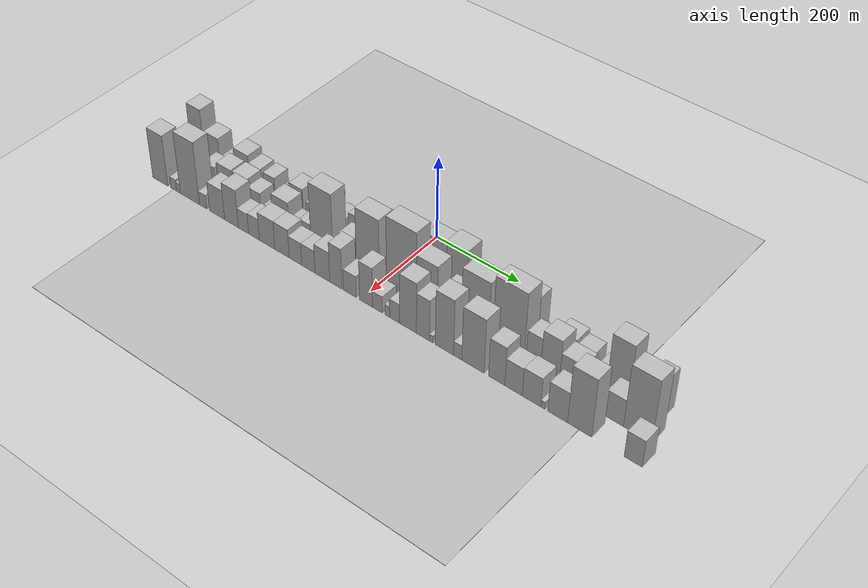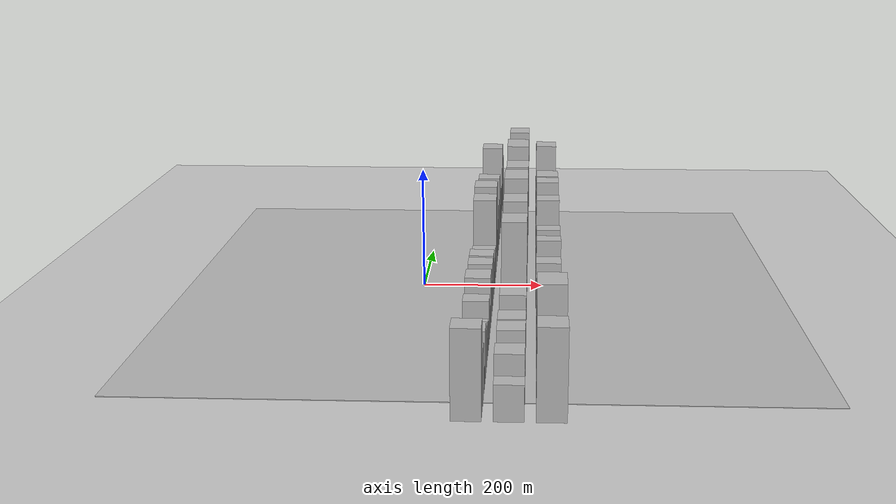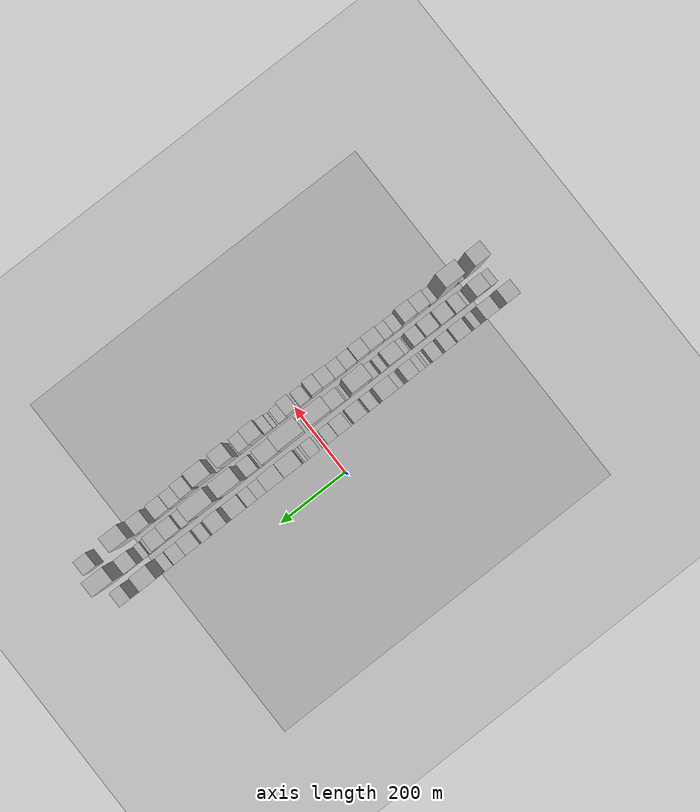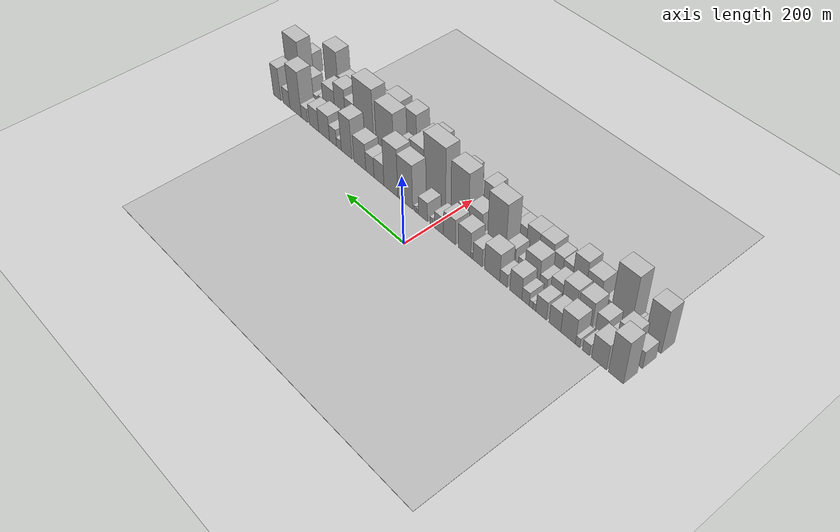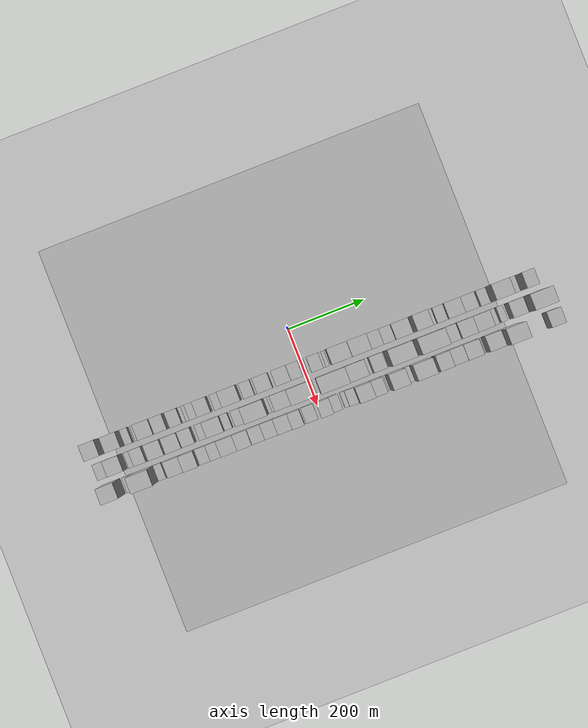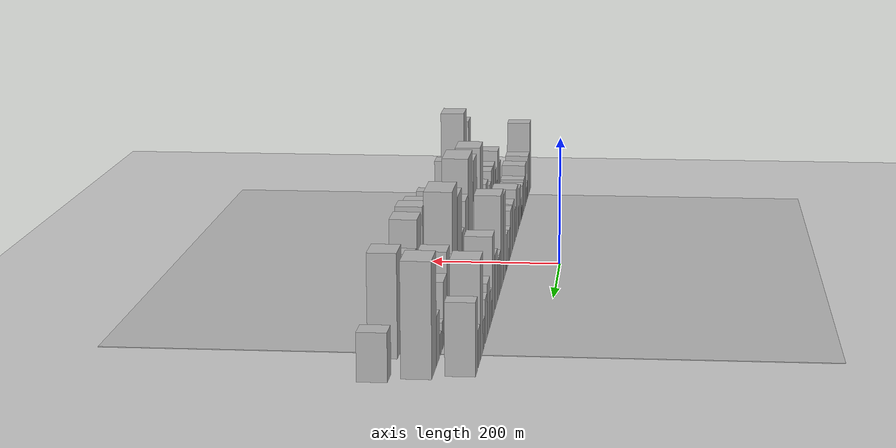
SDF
<?xml version="1.0" encoding="utf-8"?>

<sdf version="1.6">

   <world name="default">

      <gui fullscreen="0">

         <camera name="user_camera">

            <pose>-15 0 4.57585 0 0 0</pose>

            <view_controller>orbit</view_controller>

         </camera>

      </gui>

      <scene>

         <sky>

           <clouds>

             <speed>12</speed>

           </clouds>

         </sky>

         <ambient>0.4 0.4 0.4 1</ambient>

         <background>0.7 0.7 0.7 1</background>

         <shadows>1</shadows>

      </scene>

      <gravity>0 0 -9.8066</gravity>

      <magnetic_field>6e-06 2.3e-05 -4.2e-05</magnetic_field>

      <physics default="0" name="default_physics" type="ode">

         <ode>

            <solver>

               <type>quick</type>

               <iters>10</iters>

               <sor>1.0</sor>

               <use_dynamic_moi_rescaling>0</use_dynamic_moi_rescaling>

            </solver>

            <constraints>

               <cfm>0</cfm>

               <erp>0.2</erp>

               <contact_max_correcting_vel>100</contact_max_correcting_vel>

               <contact_surface_layer>0.001</contact_surface_layer>

            </constraints>

         </ode>

         <max_step_size>0.004</max_step_size>

         <real_time_factor>1</real_time_factor>

         <real_time_update_rate>250</real_time_update_rate>

      </physics>

      <light name="sun" type="directional">

         <cast_shadows>1</cast_shadows>

         <pose>0 0 10 0 0 0</pose>

         <diffuse>0.8 0.8 0.8 1</diffuse>

         <specular>0.2 0.2 0.2 1</specular>

         <attenuation>

            <range>1000</range>

            <constant>0.9</constant>

            <linear>0.01</linear>

            <quadratic>0.001</quadratic>

         </attenuation>

         <direction>-0.5 0.1 -0.9</direction>

      </light>

      <include>

         <name>ground_plane_1</name>

         <uri>model://HANNAS_ground_plane</uri>

         <pose>0 0 0  0 0 0</pose>

      </include>

      <include>

         <name>ground_plane_2</name>

         <uri>model://HANNAS_ground_plane</uri>

         <pose>100 0 0  0 0 0</pose>

      </include>

      <model name="building_1">

         <static>1</static>

         <pose frame="">100.0000 -540.5387 0 0.000000 0.000000 0.000000</pose>

         <link name="link">

            <pose frame="">0 0 63.00 0 0 0</pose>

            <collision name="collision">

               <geometry>

                  <box>

                     <size>40.0000 38.9227 126.0000</size>

                  </box>

               </geometry>

               <max_contacts>10</max_contacts>

               <surface>

                  <contact>

                     <ode/>

                  </contact>

                  <bounce/>

                  <friction>

                     <torsional>

                        <ode/>

                     </torsional>

                     <ode/>

                  </friction>

               </surface>

            </collision>

            <visual name="visual">

               <cast_shadows>0</cast_shadows>

               <geometry>

                  <box>

                     <size>40.0000 38.9227 126.0000</size>

                  </box>

               </geometry>

               <material>

                  <script>

                     <uri>model://HANNAS_wall/materials/scripts</uri>

                     <uri>model://HANNAS_wall/materials/textures</uri>

                     <name>vrc/HANNAS_wall</name>

                  </script>

               </material>

            </visual>

            <self_collide>0</self_collide>

            <enable_wind>0</enable_wind>

            <kinematic>0</kinematic>

         </link>

      </model>

      <model name="building_2">

         <static>1</static>

         <pose frame="">100.0000 -495.9135 0 0.000000 0.000000 0.000000</pose>

         <link name="link">

            <pose frame="">0 0 37.50 0 0 0</pose>

            <collision name="collision">

               <geometry>

                  <box>

                     <size>40.0000 40.3277 75.0000</size>

                  </box>

               </geometry>

               <max_contacts>10</max_contacts>

               <surface>

                  <contact>

                     <ode/>

                  </contact>

                  <bounce/>

                  <friction>

                     <torsional>

                        <ode/>

                     </torsional>

                     <ode/>

                  </friction>

               </surface>

            </collision>

            <visual name="visual">

               <cast_shadows>0</cast_shadows>

               <geometry>

                  <box>

                     <size>40.0000 40.3277 75.0000</size>

                  </box>

               </geometry>

               <material>

                  <script>

                     <uri>model://HANNAS_wall/materials/scripts</uri>

                     <uri>model://HANNAS_wall/materials/textures</uri>

                     <name>vrc/HANNAS_wall</name>

                  </script>

               </material>

            </visual>

            <self_collide>0</self_collide>

            <enable_wind>0</enable_wind>

            <kinematic>0</kinematic>

         </link>

      </model>

      <model name="building_3">

         <static>1</static>

         <pose frame="">100.0000 -461.0512 0 0.000000 0.000000 0.000000</pose>

         <link name="link">

            <pose frame="">0 0 16.50 0 0 0</pose>

            <collision name="collision">

               <geometry>

                  <box>

                     <size>40.0000 19.3968 33.0000</size>

                  </box>

               </geometry>

               <max_contacts>10</max_contacts>

               <surface>

                  <contact>

                     <ode/>

                  </contact>

                  <bounce/>

                  <friction>

                     <torsional>

                        <ode/>

                     </torsional>

                     <ode/>

                  </friction>

               </surface>

            </collision>

            <visual name="visual">

               <cast_shadows>0</cast_shadows>

               <geometry>

                  <box>

                     <size>40.0000 19.3968 33.0000</size>

                  </box>

               </geometry>

               <material>

                  <script>

                     <uri>model://HANNAS_wall/materials/scripts</uri>

                     <uri>model://HANNAS_wall/materials/textures</uri>

                     <name>vrc/HANNAS_wall</name>

                  </script>

               </material>

            </visual>

            <self_collide>0</self_collide>

            <enable_wind>0</enable_wind>

            <kinematic>0</kinematic>

         </link>

      </model>

      <model name="building_4">

         <static>1</static>

         <pose frame="">100.0000 -438.2923 0 0.000000 0.000000 0.000000</pose>

         <link name="link">

            <pose frame="">0 0 13.50 0 0 0</pose>

            <collision name="collision">

               <geometry>

                  <box>

                     <size>40.0000 12.1210 27.0000</size>

                  </box>

               </geometry>

               <max_contacts>10</max_contacts>

               <surface>

                  <contact>

                     <ode/>

                  </contact>

                  <bounce/>

                  <friction>

                     <torsional>

                        <ode/>

                     </torsional>

                     <ode/>

                  </friction>

               </surface>

            </collision>

            <visual name="visual">

               <cast_shadows>0</cast_shadows>

               <geometry>

                  <box>

                     <size>40.0000 12.1210 27.0000</size>

                  </box>

               </geometry>

               <material>

                  <script>

                     <uri>model://HANNAS_wall/materials/scripts</uri>

                     <uri>model://HANNAS_wall/materials/textures</uri>

                     <name>vrc/HANNAS_wall</name>

                  </script>

               </material>

            </visual>

            <self_collide>0</self_collide>

            <enable_wind>0</enable_wind>

            <kinematic>0</kinematic>

         </link>

      </model>

      <model name="building_5">

         <static>1</static>

         <pose frame="">100.0000 -411.9561 0 0.000000 0.000000 0.000000</pose>

         <link name="link">

            <pose frame="">0 0 37.50 0 0 0</pose>

            <collision name="collision">

               <geometry>

                  <box>

                     <size>40.0000 40.5515 75.0000</size>

                  </box>

               </geometry>

               <max_contacts>10</max_contacts>

               <surface>

                  <contact>

                     <ode/>

                  </contact>

                  <bounce/>

                  <friction>

                     <torsional>

                        <ode/>

                     </torsional>

                     <ode/>

                  </friction>

               </surface>

            </collision>

            <visual name="visual">

               <cast_shadows>0</cast_shadows>

               <geometry>

                  <box>

                     <size>40.0000 40.5515 75.0000</size>

                  </box>

               </geometry>

               <material>

                  <script>

                     <uri>model://HANNAS_wall/materials/scripts</uri>

                     <uri>model://HANNAS_wall/materials/textures</uri>

                     <name>vrc/HANNAS_wall</name>

                  </script>

               </material>

            </visual>

            <self_collide>0</self_collide>

            <enable_wind>0</enable_wind>

            <kinematic>0</kinematic>

         </link>

      </model>

      <model name="building_6">

         <static>1</static>

         <pose frame="">100.0000 -375.1806 0 0.000000 0.000000 0.000000</pose>

         <link name="link">

            <pose frame="">0 0 28.50 0 0 0</pose>

            <collision name="collision">

               <geometry>

                  <box>

                     <size>40.0000 32.9994 57.0000</size>

                  </box>

               </geometry>

               <max_contacts>10</max_contacts>

               <surface>

                  <contact>

                     <ode/>

                  </contact>

                  <bounce/>

                  <friction>

                     <torsional>

                        <ode/>

                     </torsional>

                     <ode/>

                  </friction>

               </surface>

            </collision>

            <visual name="visual">

               <cast_shadows>0</cast_shadows>

               <geometry>

                  <box>

                     <size>40.0000 32.9994 57.0000</size>

                  </box>

               </geometry>

               <material>

                  <script>

                     <uri>model://HANNAS_wall/materials/scripts</uri>

                     <uri>model://HANNAS_wall/materials/textures</uri>

                     <name>vrc/HANNAS_wall</name>

                  </script>

               </material>

            </visual>

            <self_collide>0</self_collide>

            <enable_wind>0</enable_wind>

            <kinematic>0</kinematic>

         </link>

      </model>

      <model name="building_7">

         <static>1</static>

         <pose frame="">100.0000 -336.2837 0 0.000000 0.000000 0.000000</pose>

         <link name="link">

            <pose frame="">0 0 27.00 0 0 0</pose>

            <collision name="collision">

               <geometry>

                  <box>

                     <size>40.0000 30.7946 54.0000</size>

                  </box>

               </geometry>

               <max_contacts>10</max_contacts>

               <surface>

                  <contact>

                     <ode/>

                  </contact>

                  <bounce/>

                  <friction>

                     <torsional>

                        <ode/>

                     </torsional>

                     <ode/>

                  </friction>

               </surface>

            </collision>

            <visual name="visual">

               <cast_shadows>0</cast_shadows>

               <geometry>

                  <box>

                     <size>40.0000 30.7946 54.0000</size>

                  </box>

               </geometry>

               <material>

                  <script>

                     <uri>model://HANNAS_wall/materials/scripts</uri>

                     <uri>model://HANNAS_wall/materials/textures</uri>

                     <name>vrc/HANNAS_wall</name>

                  </script>

               </material>

            </visual>

            <self_collide>0</self_collide>

            <enable_wind>0</enable_wind>

            <kinematic>0</kinematic>

         </link>

      </model>

      <model name="building_8">

         <static>1</static>

         <pose frame="">100.0000 -316.5640 0 0.000000 0.000000 0.000000</pose>

         <link name="link">

            <pose frame="">0 0 10.50 0 0 0</pose>

            <collision name="collision">

               <geometry>

                  <box>

                     <size>40.0000 8.6448 21.0000</size>

                  </box>

               </geometry>

               <max_contacts>10</max_contacts>

               <surface>

                  <contact>

                     <ode/>

                  </contact>

                  <bounce/>

                  <friction>

                     <torsional>

                        <ode/>

                     </torsional>

                     <ode/>

                  </friction>

               </surface>

            </collision>

            <visual name="visual">

               <cast_shadows>0</cast_shadows>

               <geometry>

                  <box>

                     <size>40.0000 8.6448 21.0000</size>

                  </box>

               </geometry>

               <material>

                  <script>

                     <uri>model://HANNAS_wall/materials/scripts</uri>

                     <uri>model://HANNAS_wall/materials/textures</uri>

                     <name>vrc/HANNAS_wall</name>

                  </script>

               </material>

            </visual>

            <self_collide>0</self_collide>

            <enable_wind>0</enable_wind>

            <kinematic>0</kinematic>

         </link>

      </model>

      <model name="building_9">

         <static>1</static>

         <pose frame="">100.0000 -307.0774 0 0.000000 0.000000 0.000000</pose>

         <link name="link">

            <pose frame="">0 0 10.50 0 0 0</pose>

            <collision name="collision">

               <geometry>

                  <box>

                     <size>40.0000 10.3283 21.0000</size>

                  </box>

               </geometry>

               <max_contacts>10</max_contacts>

               <surface>

                  <contact>

                     <ode/>

                  </contact>

                  <bounce/>

                  <friction>

                     <torsional>

                        <ode/>

                     </torsional>

                     <ode/>

                  </friction>

               </surface>

            </collision>

            <visual name="visual">

               <cast_shadows>0</cast_shadows>

               <geometry>

                  <box>

                     <size>40.0000 10.3283 21.0000</size>

                  </box>

               </geometry>

               <material>

                  <script>

                     <uri>model://HANNAS_wall/materials/scripts</uri>

                     <uri>model://HANNAS_wall/materials/textures</uri>

                     <name>vrc/HANNAS_wall</name>

                  </script>

               </material>

            </visual>

            <self_collide>0</self_collide>

            <enable_wind>0</enable_wind>

            <kinematic>0</kinematic>

         </link>

      </model>

      <model name="building_10">

         <static>1</static>

         <pose frame="">100.0000 -291.0015 0 0.000000 0.000000 0.000000</pose>

         <link name="link">

            <pose frame="">0 0 19.50 0 0 0</pose>

            <collision name="collision">

               <geometry>

                  <box>

                     <size>40.0000 21.8234 39.0000</size>

                  </box>

               </geometry>

               <max_contacts>10</max_contacts>

               <surface>

                  <contact>

                     <ode/>

                  </contact>

                  <bounce/>

                  <friction>

                     <torsional>

                        <ode/>

                     </torsional>

                     <ode/>

                  </friction>

               </surface>

            </collision>

            <visual name="visual">

               <cast_shadows>0</cast_shadows>

               <geometry>

                  <box>

                     <size>40.0000 21.8234 39.0000</size>

                  </box>

               </geometry>

               <material>

                  <script>

                     <uri>model://HANNAS_wall/materials/scripts</uri>

                     <uri>model://HANNAS_wall/materials/textures</uri>

                     <name>vrc/HANNAS_wall</name>

                  </script>

               </material>

            </visual>

            <self_collide>0</self_collide>

            <enable_wind>0</enable_wind>

            <kinematic>0</kinematic>

         </link>

      </model>

      <model name="building_11">

         <static>1</static>

         <pose frame="">100.0000 -262.3739 0 0.000000 0.000000 0.000000</pose>

         <link name="link">

            <pose frame="">0 0 33.00 0 0 0</pose>

            <collision name="collision">

               <geometry>

                  <box>

                     <size>40.0000 35.4319 66.0000</size>

                  </box>

               </geometry>

               <max_contacts>10</max_contacts>

               <surface>

                  <contact>

                     <ode/>

                  </contact>

                  <bounce/>

                  <friction>

                     <torsional>

                        <ode/>

                     </torsional>

                     <ode/>

                  </friction>

               </surface>

            </collision>

            <visual name="visual">

               <cast_shadows>0</cast_shadows>

               <geometry>

                  <box>

                     <size>40.0000 35.4319 66.0000</size>

                  </box>

               </geometry>

               <material>

                  <script>

                     <uri>model://HANNAS_wall/materials/scripts</uri>

                     <uri>model://HANNAS_wall/materials/textures</uri>

                     <name>vrc/HANNAS_wall</name>

                  </script>

               </material>

            </visual>

            <self_collide>0</self_collide>

            <enable_wind>0</enable_wind>

            <kinematic>0</kinematic>

         </link>

      </model>

      <model name="building_12">

         <static>1</static>

         <pose frame="">100.0000 -225.5796 0 0.000000 0.000000 0.000000</pose>

         <link name="link">

            <pose frame="">0 0 19.50 0 0 0</pose>

            <collision name="collision">

               <geometry>

                  <box>

                     <size>40.0000 22.1568 39.0000</size>

                  </box>

               </geometry>

               <max_contacts>10</max_contacts>

               <surface>

                  <contact>

                     <ode/>

                  </contact>

                  <bounce/>

                  <friction>

                     <torsional>

                        <ode/>

                     </torsional>

                     <ode/>

                  </friction>

               </surface>

            </collision>

            <visual name="visual">

               <cast_shadows>0</cast_shadows>

               <geometry>

                  <box>

                     <size>40.0000 22.1568 39.0000</size>

                  </box>

               </geometry>

               <material>

                  <script>

                     <uri>model://HANNAS_wall/materials/scripts</uri>

                     <uri>model://HANNAS_wall/materials/textures</uri>

                     <name>vrc/HANNAS_wall</name>

                  </script>

               </material>

            </visual>

            <self_collide>0</self_collide>

            <enable_wind>0</enable_wind>

            <kinematic>0</kinematic>

         </link>

      </model>

      <model name="building_13">

         <static>1</static>

         <pose frame="">100.0000 -191.0283 0 0.000000 0.000000 0.000000</pose>

         <link name="link">

            <pose frame="">0 0 40.50 0 0 0</pose>

            <collision name="collision">

               <geometry>

                  <box>

                     <size>40.0000 46.9458 81.0000</size>

                  </box>

               </geometry>

               <max_contacts>10</max_contacts>

               <surface>

                  <contact>

                     <ode/>

                  </contact>

                  <bounce/>

                  <friction>

                     <torsional>

                        <ode/>

                     </torsional>

                     <ode/>

                  </friction>

               </surface>

            </collision>

            <visual name="visual">

               <cast_shadows>0</cast_shadows>

               <geometry>

                  <box>

                     <size>40.0000 46.9458 81.0000</size>

                  </box>

               </geometry>

               <material>

                  <script>

                     <uri>model://HANNAS_wall/materials/scripts</uri>

                     <uri>model://HANNAS_wall/materials/textures</uri>

                     <name>vrc/HANNAS_wall</name>

                  </script>

               </material>

            </visual>

            <self_collide>0</self_collide>

            <enable_wind>0</enable_wind>

            <kinematic>0</kinematic>

         </link>

      </model>

      <model name="building_14">

         <static>1</static>

         <pose frame="">100.0000 -146.1428 0 0.000000 0.000000 0.000000</pose>

         <link name="link">

            <pose frame="">0 0 27.00 0 0 0</pose>

            <collision name="collision">

               <geometry>

                  <box>

                     <size>40.0000 28.8254 54.0000</size>

                  </box>

               </geometry>

               <max_contacts>10</max_contacts>

               <surface>

                  <contact>

                     <ode/>

                  </contact>

                  <bounce/>

                  <friction>

                     <torsional>

                        <ode/>

                     </torsional>

                     <ode/>

                  </friction>

               </surface>

            </collision>

            <visual name="visual">

               <cast_shadows>0</cast_shadows>

               <geometry>

                  <box>

                     <size>40.0000 28.8254 54.0000</size>

                  </box>

               </geometry>

               <material>

                  <script>

                     <uri>model://HANNAS_wall/materials/scripts</uri>

                     <uri>model://HANNAS_wall/materials/textures</uri>

                     <name>vrc/HANNAS_wall</name>

                  </script>

               </material>

            </visual>

            <self_collide>0</self_collide>

            <enable_wind>0</enable_wind>

            <kinematic>0</kinematic>

         </link>

      </model>

      <model name="building_15">

         <static>1</static>

         <pose frame="">100.0000 -128.1145 0 0.000000 0.000000 0.000000</pose>

         <link name="link">

            <pose frame="">0 0 9.00 0 0 0</pose>

            <collision name="collision">

               <geometry>

                  <box>

                     <size>40.0000 7.2312 18.0000</size>

                  </box>

               </geometry>

               <max_contacts>10</max_contacts>

               <surface>

                  <contact>

                     <ode/>

                  </contact>

                  <bounce/>

                  <friction>

                     <torsional>

                        <ode/>

                     </torsional>

                     <ode/>

                  </friction>

               </surface>

            </collision>

            <visual name="visual">

               <cast_shadows>0</cast_shadows>

               <geometry>

                  <box>

                     <size>40.0000 7.2312 18.0000</size>

                  </box>

               </geometry>

               <material>

                  <script>

                     <uri>model://HANNAS_wall/materials/scripts</uri>

                     <uri>model://HANNAS_wall/materials/textures</uri>

                     <name>vrc/HANNAS_wall</name>

                  </script>

               </material>

            </visual>

            <self_collide>0</self_collide>

            <enable_wind>0</enable_wind>

            <kinematic>0</kinematic>

         </link>

      </model>

      <model name="building_16">

         <static>1</static>

         <pose frame="">100.0000 -104.6815 0 0.000000 0.000000 0.000000</pose>

         <link name="link">

            <pose frame="">0 0 37.50 0 0 0</pose>

            <collision name="collision">

               <geometry>

                  <box>

                     <size>40.0000 39.6347 75.0000</size>

                  </box>

               </geometry>

               <max_contacts>10</max_contacts>

               <surface>

                  <contact>

                     <ode/>

                  </contact>

                  <bounce/>

                  <friction>

                     <torsional>

                        <ode/>

                     </torsional>

                     <ode/>

                  </friction>

               </surface>

            </collision>

            <visual name="visual">

               <cast_shadows>0</cast_shadows>

               <geometry>

                  <box>

                     <size>40.0000 39.6347 75.0000</size>

                  </box>

               </geometry>

               <material>

                  <script>

                     <uri>model://HANNAS_wall/materials/scripts</uri>

                     <uri>model://HANNAS_wall/materials/textures</uri>

                     <name>vrc/HANNAS_wall</name>

                  </script>

               </material>

            </visual>

            <self_collide>0</self_collide>

            <enable_wind>0</enable_wind>

            <kinematic>0</kinematic>

         </link>

      </model>

      <model name="building_17">

         <static>1</static>

         <pose frame="">100.0000 -56.6008 0 0.000000 0.000000 0.000000</pose>

         <link name="link">

            <pose frame="">0 0 37.50 0 0 0</pose>

            <collision name="collision">

               <geometry>

                  <box>

                     <size>40.0000 38.5268 75.0000</size>

                  </box>

               </geometry>

               <max_contacts>10</max_contacts>

               <surface>

                  <contact>

                     <ode/>

                  </contact>

                  <bounce/>

                  <friction>

                     <torsional>

                        <ode/>

                     </torsional>

                     <ode/>

                  </friction>

               </surface>

            </collision>

            <visual name="visual">

               <cast_shadows>0</cast_shadows>

               <geometry>

                  <box>

                     <size>40.0000 38.5268 75.0000</size>

                  </box>

               </geometry>

               <material>

                  <script>

                     <uri>model://HANNAS_wall/materials/scripts</uri>

                     <uri>model://HANNAS_wall/materials/textures</uri>

                     <name>vrc/HANNAS_wall</name>

                  </script>

               </material>

            </visual>

            <self_collide>0</self_collide>

            <enable_wind>0</enable_wind>

            <kinematic>0</kinematic>

         </link>

      </model>

      <model name="building_18">

         <static>1</static>

         <pose frame="">100.0000 -22.1608 0 0.000000 0.000000 0.000000</pose>

         <link name="link">

            <pose frame="">0 0 25.50 0 0 0</pose>

            <collision name="collision">

               <geometry>

                  <box>

                     <size>40.0000 30.3531 51.0000</size>

                  </box>

               </geometry>

               <max_contacts>10</max_contacts>

               <surface>

                  <contact>

                     <ode/>

                  </contact>

                  <bounce/>

                  <friction>

                     <torsional>

                        <ode/>

                     </torsional>

                     <ode/>

                  </friction>

               </surface>

            </collision>

            <visual name="visual">

               <cast_shadows>0</cast_shadows>

               <geometry>

                  <box>

                     <size>40.0000 30.3531 51.0000</size>

                  </box>

               </geometry>

               <material>

                  <script>

                     <uri>model://HANNAS_wall/materials/scripts</uri>

                     <uri>model://HANNAS_wall/materials/textures</uri>

                     <name>vrc/HANNAS_wall</name>

                  </script>

               </material>

            </visual>

            <self_collide>0</self_collide>

            <enable_wind>0</enable_wind>

            <kinematic>0</kinematic>

         </link>

      </model>

      <model name="building_19">

         <static>1</static>

         <pose frame="">100.0000 2.8807 0 0.000000 0.000000 0.000000</pose>

         <link name="link">

            <pose frame="">0 0 12.00 0 0 0</pose>

            <collision name="collision">

               <geometry>

                  <box>

                     <size>40.0000 9.7299 24.0000</size>

                  </box>

               </geometry>

               <max_contacts>10</max_contacts>

               <surface>

                  <contact>

                     <ode/>

                  </contact>

                  <bounce/>

                  <friction>

                     <torsional>

                        <ode/>

                     </torsional>

                     <ode/>

                  </friction>

               </surface>

            </collision>

            <visual name="visual">

               <cast_shadows>0</cast_shadows>

               <geometry>

                  <box>

                     <size>40.0000 9.7299 24.0000</size>

                  </box>

               </geometry>

               <material>

                  <script>

                     <uri>model://HANNAS_wall/materials/scripts</uri>

                     <uri>model://HANNAS_wall/materials/textures</uri>

                     <name>vrc/HANNAS_wall</name>

                  </script>

               </material>

            </visual>

            <self_collide>0</self_collide>

            <enable_wind>0</enable_wind>

            <kinematic>0</kinematic>

         </link>

      </model>

      <model name="building_20">

         <static>1</static>

         <pose frame="">100.0000 31.1038 0 0.000000 0.000000 0.000000</pose>

         <link name="link">

            <pose frame="">0 0 28.50 0 0 0</pose>

            <collision name="collision">

               <geometry>

                  <box>

                     <size>40.0000 30.7164 57.0000</size>

                  </box>

               </geometry>

               <max_contacts>10</max_contacts>

               <surface>

                  <contact>

                     <ode/>

                  </contact>

                  <bounce/>

                  <friction>

                     <torsional>

                        <ode/>

                     </torsional>

                     <ode/>

                  </friction>

               </surface>

            </collision>

            <visual name="visual">

               <cast_shadows>0</cast_shadows>

               <geometry>

                  <box>

                     <size>40.0000 30.7164 57.0000</size>

                  </box>

               </geometry>

               <material>

                  <script>

                     <uri>model://HANNAS_wall/materials/scripts</uri>

                     <uri>model://HANNAS_wall/materials/textures</uri>

                     <name>vrc/HANNAS_wall</name>

                  </script>

               </material>

            </visual>

            <self_collide>0</self_collide>

            <enable_wind>0</enable_wind>

            <kinematic>0</kinematic>

         </link>

      </model>

      <model name="building_21">

         <static>1</static>

         <pose frame="">100.0000 50.1146 0 0.000000 0.000000 0.000000</pose>

         <link name="link">

            <pose frame="">0 0 7.50 0 0 0</pose>

            <collision name="collision">

               <geometry>

                  <box>

                     <size>40.0000 7.3051 15.0000</size>

                  </box>

               </geometry>

               <max_contacts>10</max_contacts>

               <surface>

                  <contact>

                     <ode/>

                  </contact>

                  <bounce/>

                  <friction>

                     <torsional>

                        <ode/>

                     </torsional>

                     <ode/>

                  </friction>

               </surface>

            </collision>

            <visual name="visual">

               <cast_shadows>0</cast_shadows>

               <geometry>

                  <box>

                     <size>40.0000 7.3051 15.0000</size>

                  </box>

               </geometry>

               <material>

                  <script>

                     <uri>model://HANNAS_wall/materials/scripts</uri>

                     <uri>model://HANNAS_wall/materials/textures</uri>

                     <name>vrc/HANNAS_wall</name>

                  </script>

               </material>

            </visual>

            <self_collide>0</self_collide>

            <enable_wind>0</enable_wind>

            <kinematic>0</kinematic>

         </link>

      </model>

      <model name="building_22">

         <static>1</static>

         <pose frame="">100.0000 58.1221 0 0.000000 0.000000 0.000000</pose>

         <link name="link">

            <pose frame="">0 0 9.00 0 0 0</pose>

            <collision name="collision">

               <geometry>

                  <box>

                     <size>40.0000 8.7098 18.0000</size>

                  </box>

               </geometry>

               <max_contacts>10</max_contacts>

               <surface>

                  <contact>

                     <ode/>

                  </contact>

                  <bounce/>

                  <friction>

                     <torsional>

                        <ode/>

                     </torsional>

                     <ode/>

                  </friction>

               </surface>

            </collision>

            <visual name="visual">

               <cast_shadows>0</cast_shadows>

               <geometry>

                  <box>

                     <size>40.0000 8.7098 18.0000</size>

                  </box>

               </geometry>

               <material>

                  <script>

                     <uri>model://HANNAS_wall/materials/scripts</uri>

                     <uri>model://HANNAS_wall/materials/textures</uri>

                     <name>vrc/HANNAS_wall</name>

                  </script>

               </material>

            </visual>

            <self_collide>0</self_collide>

            <enable_wind>0</enable_wind>

            <kinematic>0</kinematic>

         </link>

      </model>

      <model name="building_23">

         <static>1</static>

         <pose frame="">100.0000 92.1150 0 0.000000 0.000000 0.000000</pose>

         <link name="link">

            <pose frame="">0 0 66.00 0 0 0</pose>

            <collision name="collision">

               <geometry>

                  <box>

                     <size>40.0000 51.2761 132.0000</size>

                  </box>

               </geometry>

               <max_contacts>10</max_contacts>

               <surface>

                  <contact>

                     <ode/>

                  </contact>

                  <bounce/>

                  <friction>

                     <torsional>

                        <ode/>

                     </torsional>

                     <ode/>

                  </friction>

               </surface>

            </collision>

            <visual name="visual">

               <cast_shadows>0</cast_shadows>

               <geometry>

                  <box>

                     <size>40.0000 51.2761 132.0000</size>

                  </box>

               </geometry>

               <material>

                  <script>

                     <uri>model://HANNAS_wall/materials/scripts</uri>

                     <uri>model://HANNAS_wall/materials/textures</uri>

                     <name>vrc/HANNAS_wall</name>

                  </script>

               </material>

            </visual>

            <self_collide>0</self_collide>

            <enable_wind>0</enable_wind>

            <kinematic>0</kinematic>

         </link>

      </model>

      <model name="building_24">

         <static>1</static>

         <pose frame="">100.0000 142.2321 0 0.000000 0.000000 0.000000</pose>

         <link name="link">

            <pose frame="">0 0 72.00 0 0 0</pose>

            <collision name="collision">

               <geometry>

                  <box>

                     <size>40.0000 48.9580 144.0000</size>

                  </box>

               </geometry>

               <max_contacts>10</max_contacts>

               <surface>

                  <contact>

                     <ode/>

                  </contact>

                  <bounce/>

                  <friction>

                     <torsional>

                        <ode/>

                     </torsional>

                     <ode/>

                  </friction>

               </surface>

            </collision>

            <visual name="visual">

               <cast_shadows>0</cast_shadows>

               <geometry>

                  <box>

                     <size>40.0000 48.9580 144.0000</size>

                  </box>

               </geometry>

               <material>

                  <script>

                     <uri>model://HANNAS_wall/materials/scripts</uri>

                     <uri>model://HANNAS_wall/materials/textures</uri>

                     <name>vrc/HANNAS_wall</name>

                  </script>

               </material>

            </visual>

            <self_collide>0</self_collide>

            <enable_wind>0</enable_wind>

            <kinematic>0</kinematic>

         </link>

      </model>

      <model name="building_25">

         <static>1</static>

         <pose frame="">100.0000 184.4532 0 0.000000 0.000000 0.000000</pose>

         <link name="link">

            <pose frame="">0 0 31.50 0 0 0</pose>

            <collision name="collision">

               <geometry>

                  <box>

                     <size>40.0000 35.4842 63.0000</size>

                  </box>

               </geometry>

               <max_contacts>10</max_contacts>

               <surface>

                  <contact>

                     <ode/>

                  </contact>

                  <bounce/>

                  <friction>

                     <torsional>

                        <ode/>

                     </torsional>

                     <ode/>

                  </friction>

               </surface>

            </collision>

            <visual name="visual">

               <cast_shadows>0</cast_shadows>

               <geometry>

                  <box>

                     <size>40.0000 35.4842 63.0000</size>

                  </box>

               </geometry>

               <material>

                  <script>

                     <uri>model://HANNAS_wall/materials/scripts</uri>

                     <uri>model://HANNAS_wall/materials/textures</uri>

                     <name>vrc/HANNAS_wall</name>

                  </script>

               </material>

            </visual>

            <self_collide>0</self_collide>

            <enable_wind>0</enable_wind>

            <kinematic>0</kinematic>

         </link>

      </model>

      <model name="building_26">

         <static>1</static>

         <pose frame="">100.0000 217.3462 0 0.000000 0.000000 0.000000</pose>

         <link name="link">

            <pose frame="">0 0 30.00 0 0 0</pose>

            <collision name="collision">

               <geometry>

                  <box>

                     <size>40.0000 30.3018 60.0000</size>

                  </box>

               </geometry>

               <max_contacts>10</max_contacts>

               <surface>

                  <contact>

                     <ode/>

                  </contact>

                  <bounce/>

                  <friction>

                     <torsional>

                        <ode/>

                     </torsional>

                     <ode/>

                  </friction>

               </surface>

            </collision>

            <visual name="visual">

               <cast_shadows>0</cast_shadows>

               <geometry>

                  <box>

                     <size>40.0000 30.3018 60.0000</size>

                  </box>

               </geometry>

               <material>

                  <script>

                     <uri>model://HANNAS_wall/materials/scripts</uri>

                     <uri>model://HANNAS_wall/materials/textures</uri>

                     <name>vrc/HANNAS_wall</name>

                  </script>

               </material>

            </visual>

            <self_collide>0</self_collide>

            <enable_wind>0</enable_wind>

            <kinematic>0</kinematic>

         </link>

      </model>

      <model name="building_27">

         <static>1</static>

         <pose frame="">100.0000 254.6046 0 0.000000 0.000000 0.000000</pose>

         <link name="link">

            <pose frame="">0 0 40.50 0 0 0</pose>

            <collision name="collision">

               <geometry>

                  <box>

                     <size>40.0000 44.2150 81.0000</size>

                  </box>

               </geometry>

               <max_contacts>10</max_contacts>

               <surface>

                  <contact>

                     <ode/>

                  </contact>

                  <bounce/>

                  <friction>

                     <torsional>

                        <ode/>

                     </torsional>

                     <ode/>

                  </friction>

               </surface>

            </collision>

            <visual name="visual">

               <cast_shadows>0</cast_shadows>

               <geometry>

                  <box>

                     <size>40.0000 44.2150 81.0000</size>

                  </box>

               </geometry>

               <material>

                  <script>

                     <uri>model://HANNAS_wall/materials/scripts</uri>

                     <uri>model://HANNAS_wall/materials/textures</uri>

                     <name>vrc/HANNAS_wall</name>

                  </script>

               </material>

            </visual>

            <self_collide>0</self_collide>

            <enable_wind>0</enable_wind>

            <kinematic>0</kinematic>

         </link>

      </model>

      <model name="building_28">

         <static>1</static>

         <pose frame="">100.0000 304.0075 0 0.000000 0.000000 0.000000</pose>

         <link name="link">

            <pose frame="">0 0 60.00 0 0 0</pose>

            <collision name="collision">

               <geometry>

                  <box>

                     <size>40.0000 40.5909 120.0000</size>

                  </box>

               </geometry>

               <max_contacts>10</max_contacts>

               <surface>

                  <contact>

                     <ode/>

                  </contact>

                  <bounce/>

                  <friction>

                     <torsional>

                        <ode/>

                     </torsional>

                     <ode/>

                  </friction>

               </surface>

            </collision>

            <visual name="visual">

               <cast_shadows>0</cast_shadows>

               <geometry>

                  <box>

                     <size>40.0000 40.5909 120.0000</size>

                  </box>

               </geometry>

               <material>

                  <script>

                     <uri>model://HANNAS_wall/materials/scripts</uri>

                     <uri>model://HANNAS_wall/materials/textures</uri>

                     <name>vrc/HANNAS_wall</name>

                  </script>

               </material>

            </visual>

            <self_collide>0</self_collide>

            <enable_wind>0</enable_wind>

            <kinematic>0</kinematic>

         </link>

      </model>

      <model name="building_29">

         <static>1</static>

         <pose frame="">100.0000 333.1711 0 0.000000 0.000000 0.000000</pose>

         <link name="link">

            <pose frame="">0 0 15.00 0 0 0</pose>

            <collision name="collision">

               <geometry>

                  <box>

                     <size>40.0000 17.7362 30.0000</size>

                  </box>

               </geometry>

               <max_contacts>10</max_contacts>

               <surface>

                  <contact>

                     <ode/>

                  </contact>

                  <bounce/>

                  <friction>

                     <torsional>

                        <ode/>

                     </torsional>

                     <ode/>

                  </friction>

               </surface>

            </collision>

            <visual name="visual">

               <cast_shadows>0</cast_shadows>

               <geometry>

                  <box>

                     <size>40.0000 17.7362 30.0000</size>

                  </box>

               </geometry>

               <material>

                  <script>

                     <uri>model://HANNAS_wall/materials/scripts</uri>

                     <uri>model://HANNAS_wall/materials/textures</uri>

                     <name>vrc/HANNAS_wall</name>

                  </script>

               </material>

            </visual>

            <self_collide>0</self_collide>

            <enable_wind>0</enable_wind>

            <kinematic>0</kinematic>

         </link>

      </model>

      <model name="building_30">

         <static>1</static>

         <pose frame="">100.0000 355.6493 0 0.000000 0.000000 0.000000</pose>

         <link name="link">

            <pose frame="">0 0 25.50 0 0 0</pose>

            <collision name="collision">

               <geometry>

                  <box>

                     <size>40.0000 27.2202 51.0000</size>

                  </box>

               </geometry>

               <max_contacts>10</max_contacts>

               <surface>

                  <contact>

                     <ode/>

                  </contact>

                  <bounce/>

                  <friction>

                     <torsional>

                        <ode/>

                     </torsional>

                     <ode/>

                  </friction>

               </surface>

            </collision>

            <visual name="visual">

               <cast_shadows>0</cast_shadows>

               <geometry>

                  <box>

                     <size>40.0000 27.2202 51.0000</size>

                  </box>

               </geometry>

               <material>

                  <script>

                     <uri>model://HANNAS_wall/materials/scripts</uri>

                     <uri>model://HANNAS_wall/materials/textures</uri>

                     <name>vrc/HANNAS_wall</name>

                  </script>

               </material>

            </visual>

            <self_collide>0</self_collide>

            <enable_wind>0</enable_wind>

            <kinematic>0</kinematic>

         </link>

      </model>

      <model name="building_31">

         <static>1</static>

         <pose frame="">100.0000 390.4348 0 0.000000 0.000000 0.000000</pose>

         <link name="link">

            <pose frame="">0 0 37.50 0 0 0</pose>

            <collision name="collision">

               <geometry>

                  <box>

                     <size>40.0000 42.3508 75.0000</size>

                  </box>

               </geometry>

               <max_contacts>10</max_contacts>

               <surface>

                  <contact>

                     <ode/>

                  </contact>

                  <bounce/>

                  <friction>

                     <torsional>

                        <ode/>

                     </torsional>

                     <ode/>

                  </friction>

               </surface>

            </collision>

            <visual name="visual">

               <cast_shadows>0</cast_shadows>

               <geometry>

                  <box>

                     <size>40.0000 42.3508 75.0000</size>

                  </box>

               </geometry>

               <material>

                  <script>

                     <uri>model://HANNAS_wall/materials/scripts</uri>

                     <uri>model://HANNAS_wall/materials/textures</uri>

                     <name>vrc/HANNAS_wall</name>

                  </script>

               </material>

            </visual>

            <self_collide>0</self_collide>

            <enable_wind>0</enable_wind>

            <kinematic>0</kinematic>

         </link>

      </model>

      <model name="building_32">

         <static>1</static>

         <pose frame="">100.0000 430.4082 0 0.000000 0.000000 0.000000</pose>

         <link name="link">

            <pose frame="">0 0 31.50 0 0 0</pose>

            <collision name="collision">

               <geometry>

                  <box>

                     <size>40.0000 37.5960 63.0000</size>

                  </box>

               </geometry>

               <max_contacts>10</max_contacts>

               <surface>

                  <contact>

                     <ode/>

                  </contact>

                  <bounce/>

                  <friction>

                     <torsional>

                        <ode/>

                     </torsional>

                     <ode/>

                  </friction>

               </surface>

            </collision>

            <visual name="visual">

               <cast_shadows>0</cast_shadows>

               <geometry>

                  <box>

                     <size>40.0000 37.5960 63.0000</size>

                  </box>

               </geometry>

               <material>

                  <script>

                     <uri>model://HANNAS_wall/materials/scripts</uri>

                     <uri>model://HANNAS_wall/materials/textures</uri>

                     <name>vrc/HANNAS_wall</name>

                  </script>

               </material>

            </visual>

            <self_collide>0</self_collide>

            <enable_wind>0</enable_wind>

            <kinematic>0</kinematic>

         </link>

      </model>

      <model name="building_33">

         <static>1</static>

         <pose frame="">100.0000 468.7266 0 0.000000 0.000000 0.000000</pose>

         <link name="link">

            <pose frame="">0 0 21.00 0 0 0</pose>

            <collision name="collision">

               <geometry>

                  <box>

                     <size>40.0000 25.0409 42.0000</size>

                  </box>

               </geometry>

               <max_contacts>10</max_contacts>

               <surface>

                  <contact>

                     <ode/>

                  </contact>

                  <bounce/>

                  <friction>

                     <torsional>

                        <ode/>

                     </torsional>

                     <ode/>

                  </friction>

               </surface>

            </collision>

            <visual name="visual">

               <cast_shadows>0</cast_shadows>

               <geometry>

                  <box>

                     <size>40.0000 25.0409 42.0000</size>

                  </box>

               </geometry>

               <material>

                  <script>

                     <uri>model://HANNAS_wall/materials/scripts</uri>

                     <uri>model://HANNAS_wall/materials/textures</uri>

                     <name>vrc/HANNAS_wall</name>

                  </script>

               </material>

            </visual>

            <self_collide>0</self_collide>

            <enable_wind>0</enable_wind>

            <kinematic>0</kinematic>

         </link>

      </model>

      <model name="building_34">

         <static>1</static>

         <pose frame="">100.0000 504.8101 0 0.000000 0.000000 0.000000</pose>

         <link name="link">

            <pose frame="">0 0 69.00 0 0 0</pose>

            <collision name="collision">

               <geometry>

                  <box>

                     <size>40.0000 47.1262 138.0000</size>

                  </box>

               </geometry>

               <max_contacts>10</max_contacts>

               <surface>

                  <contact>

                     <ode/>

                  </contact>

                  <bounce/>

                  <friction>

                     <torsional>

                        <ode/>

                     </torsional>

                     <ode/>

                  </friction>

               </surface>

            </collision>

            <visual name="visual">

               <cast_shadows>0</cast_shadows>

               <geometry>

                  <box>

                     <size>40.0000 47.1262 138.0000</size>

                  </box>

               </geometry>

               <material>

                  <script>

                     <uri>model://HANNAS_wall/materials/scripts</uri>

                     <uri>model://HANNAS_wall/materials/textures</uri>

                     <name>vrc/HANNAS_wall</name>

                  </script>

               </material>

            </visual>

            <self_collide>0</self_collide>

            <enable_wind>0</enable_wind>

            <kinematic>0</kinematic>

         </link>

      </model>

      <model name="building_35">

         <static>1</static>

         <pose frame="">100.0000 542.4914 0 0.000000 0.000000 0.000000</pose>

         <link name="link">

            <pose frame="">0 0 25.50 0 0 0</pose>

            <collision name="collision">

               <geometry>

                  <box>

                     <size>40.0000 28.2363 51.0000</size>

                  </box>

               </geometry>

               <max_contacts>10</max_contacts>

               <surface>

                  <contact>

                     <ode/>

                  </contact>

                  <bounce/>

                  <friction>

                     <torsional>

                        <ode/>

                     </torsional>

                     <ode/>

                  </friction>

               </surface>

            </collision>

            <visual name="visual">

               <cast_shadows>0</cast_shadows>

               <geometry>

                  <box>

                     <size>40.0000 28.2363 51.0000</size>

                  </box>

               </geometry>

               <material>

                  <script>

                     <uri>model://HANNAS_wall/materials/scripts</uri>

                     <uri>model://HANNAS_wall/materials/textures</uri>

                     <name>vrc/HANNAS_wall</name>

                  </script>

               </material>

            </visual>

            <self_collide>0</self_collide>

            <enable_wind>0</enable_wind>

            <kinematic>0</kinematic>

         </link>

      </model>

      <model name="building_36">

         <static>1</static>

         <pose frame="">100.0000 581.3271 0 0.000000 0.000000 0.000000</pose>

         <link name="link">

            <pose frame="">0 0 49.50 0 0 0</pose>

            <collision name="collision">

               <geometry>

                  <box>

                     <size>40.0000 31.4352 99.0000</size>

                  </box>

               </geometry>

               <max_contacts>10</max_contacts>

               <surface>

                  <contact>

                     <ode/>

                  </contact>

                  <bounce/>

                  <friction>

                     <torsional>

                        <ode/>

                     </torsional>

                     <ode/>

                  </friction>

               </surface>

            </collision>

            <visual name="visual">

               <cast_shadows>0</cast_shadows>

               <geometry>

                  <box>

                     <size>40.0000 31.4352 99.0000</size>

                  </box>

               </geometry>

               <material>

                  <script>

                     <uri>model://HANNAS_wall/materials/scripts</uri>

                     <uri>model://HANNAS_wall/materials/textures</uri>

                     <name>vrc/HANNAS_wall</name>

                  </script>

               </material>

            </visual>

            <self_collide>0</self_collide>

            <enable_wind>0</enable_wind>

            <kinematic>0</kinematic>

         </link>

      </model>

      <model name="building_37">

         <static>1</static>

         <pose frame="">155.0000 -545.2110 0 0.000000 0.000000 0.000000</pose>

         <link name="link">

            <pose frame="">0 0 25.50 0 0 0</pose>

            <collision name="collision">

               <geometry>

                  <box>

                     <size>40.0000 29.5780 51.0000</size>

                  </box>

               </geometry>

               <max_contacts>10</max_contacts>

               <surface>

                  <contact>

                     <ode/>

                  </contact>

                  <bounce/>

                  <friction>

                     <torsional>

                        <ode/>

                     </torsional>

                     <ode/>

                  </friction>

               </surface>

            </collision>

            <visual name="visual">

               <cast_shadows>0</cast_shadows>

               <geometry>

                  <box>

                     <size>40.0000 29.5780 51.0000</size>

                  </box>

               </geometry>

               <material>

                  <script>

                     <uri>model://HANNAS_wall/materials/scripts</uri>

                     <uri>model://HANNAS_wall/materials/textures</uri>

                     <name>vrc/HANNAS_wall</name>

                  </script>

               </material>

            </visual>

            <self_collide>0</self_collide>

            <enable_wind>0</enable_wind>

            <kinematic>0</kinematic>

         </link>

      </model>

      <model name="building_38">

         <static>1</static>

         <pose frame="">155.0000 -509.9299 0 0.000000 0.000000 0.000000</pose>

         <link name="link">

            <pose frame="">0 0 40.50 0 0 0</pose>

            <collision name="collision">

               <geometry>

                  <box>

                     <size>40.0000 40.9843 81.0000</size>

                  </box>

               </geometry>

               <max_contacts>10</max_contacts>

               <surface>

                  <contact>

                     <ode/>

                  </contact>

                  <bounce/>

                  <friction>

                     <torsional>

                        <ode/>

                     </torsional>

                     <ode/>

                  </friction>

               </surface>

            </collision>

            <visual name="visual">

               <cast_shadows>0</cast_shadows>

               <geometry>

                  <box>

                     <size>40.0000 40.9843 81.0000</size>

                  </box>

               </geometry>

               <material>

                  <script>

                     <uri>model://HANNAS_wall/materials/scripts</uri>

                     <uri>model://HANNAS_wall/materials/textures</uri>

                     <name>vrc/HANNAS_wall</name>

                  </script>

               </material>

            </visual>

            <self_collide>0</self_collide>

            <enable_wind>0</enable_wind>

            <kinematic>0</kinematic>

         </link>

      </model>

      <model name="building_39">

         <static>1</static>

         <pose frame="">155.0000 -474.0493 0 0.000000 0.000000 0.000000</pose>

         <link name="link">

            <pose frame="">0 0 15.00 0 0 0</pose>

            <collision name="collision">

               <geometry>

                  <box>

                     <size>40.0000 16.7770 30.0000</size>

                  </box>

               </geometry>

               <max_contacts>10</max_contacts>

               <surface>

                  <contact>

                     <ode/>

                  </contact>

                  <bounce/>

                  <friction>

                     <torsional>

                        <ode/>

                     </torsional>

                     <ode/>

                  </friction>

               </surface>

            </collision>

            <visual name="visual">

               <cast_shadows>0</cast_shadows>

               <geometry>

                  <box>

                     <size>40.0000 16.7770 30.0000</size>

                  </box>

               </geometry>

               <material>

                  <script>

                     <uri>model://HANNAS_wall/materials/scripts</uri>

                     <uri>model://HANNAS_wall/materials/textures</uri>

                     <name>vrc/HANNAS_wall</name>

                  </script>

               </material>

            </visual>

            <self_collide>0</self_collide>

            <enable_wind>0</enable_wind>

            <kinematic>0</kinematic>

         </link>

      </model>

      <model name="building_40">

         <static>1</static>

         <pose frame="">155.0000 -449.9052 0 0.000000 0.000000 0.000000</pose>

         <link name="link">

            <pose frame="">0 0 28.50 0 0 0</pose>

            <collision name="collision">

               <geometry>

                  <box>

                     <size>40.0000 31.5112 57.0000</size>

                  </box>

               </geometry>

               <max_contacts>10</max_contacts>

               <surface>

                  <contact>

                     <ode/>

                  </contact>

                  <bounce/>

                  <friction>

                     <torsional>

                        <ode/>

                     </torsional>

                     <ode/>

                  </friction>

               </surface>

            </collision>

            <visual name="visual">

               <cast_shadows>0</cast_shadows>

               <geometry>

                  <box>

                     <size>40.0000 31.5112 57.0000</size>

                  </box>

               </geometry>

               <material>

                  <script>

                     <uri>model://HANNAS_wall/materials/scripts</uri>

                     <uri>model://HANNAS_wall/materials/textures</uri>

                     <name>vrc/HANNAS_wall</name>

                  </script>

               </material>

            </visual>

            <self_collide>0</self_collide>

            <enable_wind>0</enable_wind>

            <kinematic>0</kinematic>

         </link>

      </model>

      <model name="building_41">

         <static>1</static>

         <pose frame="">155.0000 -405.9209 0 0.000000 0.000000 0.000000</pose>

         <link name="link">

            <pose frame="">0 0 37.50 0 0 0</pose>

            <collision name="collision">

               <geometry>

                  <box>

                     <size>40.0000 40.4575 75.0000</size>

                  </box>

               </geometry>

               <max_contacts>10</max_contacts>

               <surface>

                  <contact>

                     <ode/>

                  </contact>

                  <bounce/>

                  <friction>

                     <torsional>

                        <ode/>

                     </torsional>

                     <ode/>

                  </friction>

               </surface>

            </collision>

            <visual name="visual">

               <cast_shadows>0</cast_shadows>

               <geometry>

                  <box>

                     <size>40.0000 40.4575 75.0000</size>

                  </box>

               </geometry>

               <material>

                  <script>

                     <uri>model://HANNAS_wall/materials/scripts</uri>

                     <uri>model://HANNAS_wall/materials/textures</uri>

                     <name>vrc/HANNAS_wall</name>

                  </script>

               </material>

            </visual>

            <self_collide>0</self_collide>

            <enable_wind>0</enable_wind>

            <kinematic>0</kinematic>

         </link>

      </model>

      <model name="building_42">

         <static>1</static>

         <pose frame="">155.0000 -361.5441 0 0.000000 0.000000 0.000000</pose>

         <link name="link">

            <pose frame="">0 0 37.50 0 0 0</pose>

            <collision name="collision">

               <geometry>

                  <box>

                     <size>40.0000 40.2959 75.0000</size>

                  </box>

               </geometry>

               <max_contacts>10</max_contacts>

               <surface>

                  <contact>

                     <ode/>

                  </contact>

                  <bounce/>

                  <friction>

                     <torsional>

                        <ode/>

                     </torsional>

                     <ode/>

                  </friction>

               </surface>

            </collision>

            <visual name="visual">

               <cast_shadows>0</cast_shadows>

               <geometry>

                  <box>

                     <size>40.0000 40.2959 75.0000</size>

                  </box>

               </geometry>

               <material>

                  <script>

                     <uri>model://HANNAS_wall/materials/scripts</uri>

                     <uri>model://HANNAS_wall/materials/textures</uri>

                     <name>vrc/HANNAS_wall</name>

                  </script>

               </material>

            </visual>

            <self_collide>0</self_collide>

            <enable_wind>0</enable_wind>

            <kinematic>0</kinematic>

         </link>

      </model>

      <model name="building_43">

         <static>1</static>

         <pose frame="">155.0000 -324.6155 0 0.000000 0.000000 0.000000</pose>

         <link name="link">

            <pose frame="">0 0 28.50 0 0 0</pose>

            <collision name="collision">

               <geometry>

                  <box>

                     <size>40.0000 33.5614 57.0000</size>

                  </box>

               </geometry>

               <max_contacts>10</max_contacts>

               <surface>

                  <contact>

                     <ode/>

                  </contact>

                  <bounce/>

                  <friction>

                     <torsional>

                        <ode/>

                     </torsional>

                     <ode/>

                  </friction>

               </surface>

            </collision>

            <visual name="visual">

               <cast_shadows>0</cast_shadows>

               <geometry>

                  <box>

                     <size>40.0000 33.5614 57.0000</size>

                  </box>

               </geometry>

               <material>

                  <script>

                     <uri>model://HANNAS_wall/materials/scripts</uri>

                     <uri>model://HANNAS_wall/materials/textures</uri>

                     <name>vrc/HANNAS_wall</name>

                  </script>

               </material>

            </visual>

            <self_collide>0</self_collide>

            <enable_wind>0</enable_wind>

            <kinematic>0</kinematic>

         </link>

      </model>

      <model name="building_44">

         <static>1</static>

         <pose frame="">155.0000 -287.1932 0 0.000000 0.000000 0.000000</pose>

         <link name="link">

            <pose frame="">0 0 18.00 0 0 0</pose>

            <collision name="collision">

               <geometry>

                  <box>

                     <size>40.0000 21.2831 36.0000</size>

                  </box>

               </geometry>

               <max_contacts>10</max_contacts>

               <surface>

                  <contact>

                     <ode/>

                  </contact>

                  <bounce/>

                  <friction>

                     <torsional>

                        <ode/>

                     </torsional>

                     <ode/>

                  </friction>

               </surface>

            </collision>

            <visual name="visual">

               <cast_shadows>0</cast_shadows>

               <geometry>

                  <box>

                     <size>40.0000 21.2831 36.0000</size>

                  </box>

               </geometry>

               <material>

                  <script>

                     <uri>model://HANNAS_wall/materials/scripts</uri>

                     <uri>model://HANNAS_wall/materials/textures</uri>

                     <name>vrc/HANNAS_wall</name>

                  </script>

               </material>

            </visual>

            <self_collide>0</self_collide>

            <enable_wind>0</enable_wind>

            <kinematic>0</kinematic>

         </link>

      </model>

      <model name="building_45">

         <static>1</static>

         <pose frame="">155.0000 -254.1375 0 0.000000 0.000000 0.000000</pose>

         <link name="link">

            <pose frame="">0 0 37.50 0 0 0</pose>

            <collision name="collision">

               <geometry>

                  <box>

                     <size>40.0000 44.8283 75.0000</size>

                  </box>

               </geometry>

               <max_contacts>10</max_contacts>

               <surface>

                  <contact>

                     <ode/>

                  </contact>

                  <bounce/>

                  <friction>

                     <torsional>

                        <ode/>

                     </torsional>

                     <ode/>

                  </friction>

               </surface>

            </collision>

            <visual name="visual">

               <cast_shadows>0</cast_shadows>

               <geometry>

                  <box>

                     <size>40.0000 44.8283 75.0000</size>

                  </box>

               </geometry>

               <material>

                  <script>

                     <uri>model://HANNAS_wall/materials/scripts</uri>

                     <uri>model://HANNAS_wall/materials/textures</uri>

                     <name>vrc/HANNAS_wall</name>

                  </script>

               </material>

            </visual>

            <self_collide>0</self_collide>

            <enable_wind>0</enable_wind>

            <kinematic>0</kinematic>

         </link>

      </model>

      <model name="building_46">

         <static>1</static>

         <pose frame="">155.0000 -221.7495 0 0.000000 0.000000 0.000000</pose>

         <link name="link">

            <pose frame="">0 0 18.00 0 0 0</pose>

            <collision name="collision">

               <geometry>

                  <box>

                     <size>40.0000 19.9477 36.0000</size>

                  </box>

               </geometry>

               <max_contacts>10</max_contacts>

               <surface>

                  <contact>

                     <ode/>

                  </contact>

                  <bounce/>

                  <friction>

                     <torsional>

                        <ode/>

                     </torsional>

                     <ode/>

                  </friction>

               </surface>

            </collision>

            <visual name="visual">

               <cast_shadows>0</cast_shadows>

               <geometry>

                  <box>

                     <size>40.0000 19.9477 36.0000</size>

                  </box>

               </geometry>

               <material>

                  <script>

                     <uri>model://HANNAS_wall/materials/scripts</uri>

                     <uri>model://HANNAS_wall/materials/textures</uri>

                     <name>vrc/HANNAS_wall</name>

                  </script>

               </material>

            </visual>

            <self_collide>0</self_collide>

            <enable_wind>0</enable_wind>

            <kinematic>0</kinematic>

         </link>

      </model>

      <model name="building_47">

         <static>1</static>

         <pose frame="">155.0000 -189.0894 0 0.000000 0.000000 0.000000</pose>

         <link name="link">

            <pose frame="">0 0 25.50 0 0 0</pose>

            <collision name="collision">

               <geometry>

                  <box>

                     <size>40.0000 29.3726 51.0000</size>

                  </box>

               </geometry>

               <max_contacts>10</max_contacts>

               <surface>

                  <contact>

                     <ode/>

                  </contact>

                  <bounce/>

                  <friction>

                     <torsional>

                        <ode/>

                     </torsional>

                     <ode/>

                  </friction>

               </surface>

            </collision>

            <visual name="visual">

               <cast_shadows>0</cast_shadows>

               <geometry>

                  <box>

                     <size>40.0000 29.3726 51.0000</size>

                  </box>

               </geometry>

               <material>

                  <script>

                     <uri>model://HANNAS_wall/materials/scripts</uri>

                     <uri>model://HANNAS_wall/materials/textures</uri>

                     <name>vrc/HANNAS_wall</name>

                  </script>

               </material>

            </visual>

            <self_collide>0</self_collide>

            <enable_wind>0</enable_wind>

            <kinematic>0</kinematic>

         </link>

      </model>

      <model name="building_48">

         <static>1</static>

         <pose frame="">155.0000 -145.8707 0 0.000000 0.000000 0.000000</pose>

         <link name="link">

            <pose frame="">0 0 79.50 0 0 0</pose>

            <collision name="collision">

               <geometry>

                  <box>

                     <size>40.0000 57.0646 159.0000</size>

                  </box>

               </geometry>

               <max_contacts>10</max_contacts>

               <surface>

                  <contact>

                     <ode/>

                  </contact>

                  <bounce/>

                  <friction>

                     <torsional>

                        <ode/>

                     </torsional>

                     <ode/>

                  </friction>

               </surface>

            </collision>

            <visual name="visual">

               <cast_shadows>0</cast_shadows>

               <geometry>

                  <box>

                     <size>40.0000 57.0646 159.0000</size>

                  </box>

               </geometry>

               <material>

                  <script>

                     <uri>model://HANNAS_wall/materials/scripts</uri>

                     <uri>model://HANNAS_wall/materials/textures</uri>

                     <name>vrc/HANNAS_wall</name>

                  </script>

               </material>

            </visual>

            <self_collide>0</self_collide>

            <enable_wind>0</enable_wind>

            <kinematic>0</kinematic>

         </link>

      </model>

      <model name="building_49">

         <static>1</static>

         <pose frame="">155.0000 -113.1557 0 0.000000 0.000000 0.000000</pose>

         <link name="link">

            <pose frame="">0 0 9.00 0 0 0</pose>

            <collision name="collision">

               <geometry>

                  <box>

                     <size>40.0000 8.3654 18.0000</size>

                  </box>

               </geometry>

               <max_contacts>10</max_contacts>

               <surface>

                  <contact>

                     <ode/>

                  </contact>

                  <bounce/>

                  <friction>

                     <torsional>

                        <ode/>

                     </torsional>

                     <ode/>

                  </friction>

               </surface>

            </collision>

            <visual name="visual">

               <cast_shadows>0</cast_shadows>

               <geometry>

                  <box>

                     <size>40.0000 8.3654 18.0000</size>

                  </box>

               </geometry>

               <material>

                  <script>

                     <uri>model://HANNAS_wall/materials/scripts</uri>

                     <uri>model://HANNAS_wall/materials/textures</uri>

                     <name>vrc/HANNAS_wall</name>

                  </script>

               </material>

            </visual>

            <self_collide>0</self_collide>

            <enable_wind>0</enable_wind>

            <kinematic>0</kinematic>

         </link>

      </model>

      <model name="building_50">

         <static>1</static>

         <pose frame="">155.0000 -104.8745 0 0.000000 0.000000 0.000000</pose>

         <link name="link">

            <pose frame="">0 0 9.00 0 0 0</pose>

            <collision name="collision">

               <geometry>

                  <box>

                     <size>40.0000 8.1972 18.0000</size>

                  </box>

               </geometry>

               <max_contacts>10</max_contacts>

               <surface>

                  <contact>

                     <ode/>

                  </contact>

                  <bounce/>

                  <friction>

                     <torsional>

                        <ode/>

                     </torsional>

                     <ode/>

                  </friction>

               </surface>

            </collision>

            <visual name="visual">

               <cast_shadows>0</cast_shadows>

               <geometry>

                  <box>

                     <size>40.0000 8.1972 18.0000</size>

                  </box>

               </geometry>

               <material>

                  <script>

                     <uri>model://HANNAS_wall/materials/scripts</uri>

                     <uri>model://HANNAS_wall/materials/textures</uri>

                     <name>vrc/HANNAS_wall</name>

                  </script>

               </material>

            </visual>

            <self_collide>0</self_collide>

            <enable_wind>0</enable_wind>

            <kinematic>0</kinematic>

         </link>

      </model>

      <model name="building_51">

         <static>1</static>

         <pose frame="">155.0000 -79.0919 0 0.000000 0.000000 0.000000</pose>

         <link name="link">

            <pose frame="">0 0 37.50 0 0 0</pose>

            <collision name="collision">

               <geometry>

                  <box>

                     <size>40.0000 43.3679 75.0000</size>

                  </box>

               </geometry>

               <max_contacts>10</max_contacts>

               <surface>

                  <contact>

                     <ode/>

                  </contact>

                  <bounce/>

                  <friction>

                     <torsional>

                        <ode/>

                     </torsional>

                     <ode/>

                  </friction>

               </surface>

            </collision>

            <visual name="visual">

               <cast_shadows>0</cast_shadows>

               <geometry>

                  <box>

                     <size>40.0000 43.3679 75.0000</size>

                  </box>

               </geometry>

               <material>

                  <script>

                     <uri>model://HANNAS_wall/materials/scripts</uri>

                     <uri>model://HANNAS_wall/materials/textures</uri>

                     <name>vrc/HANNAS_wall</name>

                  </script>

               </material>

            </visual>

            <self_collide>0</self_collide>

            <enable_wind>0</enable_wind>

            <kinematic>0</kinematic>

         </link>

      </model>

      <model name="building_52">

         <static>1</static>

         <pose frame="">155.0000 -28.5713 0 0.000000 0.000000 0.000000</pose>

         <link name="link">

            <pose frame="">0 0 81.00 0 0 0</pose>

            <collision name="collision">

               <geometry>

                  <box>

                     <size>40.0000 57.6732 162.0000</size>

                  </box>

               </geometry>

               <max_contacts>10</max_contacts>

               <surface>

                  <contact>

                     <ode/>

                  </contact>

                  <bounce/>

                  <friction>

                     <torsional>

                        <ode/>

                     </torsional>

                     <ode/>

                  </friction>

               </surface>

            </collision>

            <visual name="visual">

               <cast_shadows>0</cast_shadows>

               <geometry>

                  <box>

                     <size>40.0000 57.6732 162.0000</size>

                  </box>

               </geometry>

               <material>

                  <script>

                     <uri>model://HANNAS_wall/materials/scripts</uri>

                     <uri>model://HANNAS_wall/materials/textures</uri>

                     <name>vrc/HANNAS_wall</name>

                  </script>

               </material>

            </visual>

            <self_collide>0</self_collide>

            <enable_wind>0</enable_wind>

            <kinematic>0</kinematic>

         </link>

      </model>

      <model name="building_53">

         <static>1</static>

         <pose frame="">155.0000 4.5576 0 0.000000 0.000000 0.000000</pose>

         <link name="link">

            <pose frame="">0 0 10.50 0 0 0</pose>

            <collision name="collision">

               <geometry>

                  <box>

                     <size>40.0000 8.5847 21.0000</size>

                  </box>

               </geometry>

               <max_contacts>10</max_contacts>

               <surface>

                  <contact>

                     <ode/>

                  </contact>

                  <bounce/>

                  <friction>

                     <torsional>

                        <ode/>

                     </torsional>

                     <ode/>

                  </friction>

               </surface>

            </collision>

            <visual name="visual">

               <cast_shadows>0</cast_shadows>

               <geometry>

                  <box>

                     <size>40.0000 8.5847 21.0000</size>

                  </box>

               </geometry>

               <material>

                  <script>

                     <uri>model://HANNAS_wall/materials/scripts</uri>

                     <uri>model://HANNAS_wall/materials/textures</uri>

                     <name>vrc/HANNAS_wall</name>

                  </script>

               </material>

            </visual>

            <self_collide>0</self_collide>

            <enable_wind>0</enable_wind>

            <kinematic>0</kinematic>

         </link>

      </model>

      <model name="building_54">

         <static>1</static>

         <pose frame="">155.0000 54.0889 0 0.000000 0.000000 0.000000</pose>

         <link name="link">

            <pose frame="">0 0 91.50 0 0 0</pose>

            <collision name="collision">

               <geometry>

                  <box>

                     <size>40.0000 72.4778 183.0000</size>

                  </box>

               </geometry>

               <max_contacts>10</max_contacts>

               <surface>

                  <contact>

                     <ode/>

                  </contact>

                  <bounce/>

                  <friction>

                     <torsional>

                        <ode/>

                     </torsional>

                     <ode/>

                  </friction>

               </surface>

            </collision>

            <visual name="visual">

               <cast_shadows>0</cast_shadows>

               <geometry>

                  <box>

                     <size>40.0000 72.4778 183.0000</size>

                  </box>

               </geometry>

               <material>

                  <script>

                     <uri>model://HANNAS_wall/materials/scripts</uri>

                     <uri>model://HANNAS_wall/materials/textures</uri>

                     <name>vrc/HANNAS_wall</name>

                  </script>

               </material>

            </visual>

            <self_collide>0</self_collide>

            <enable_wind>0</enable_wind>

            <kinematic>0</kinematic>

         </link>

      </model>

      <model name="building_55">

         <static>1</static>

         <pose frame="">155.0000 115.5524 0 0.000000 0.000000 0.000000</pose>

         <link name="link">

            <pose frame="">0 0 64.50 0 0 0</pose>

            <collision name="collision">

               <geometry>

                  <box>

                     <size>40.0000 50.4492 129.0000</size>

                  </box>

               </geometry>

               <max_contacts>10</max_contacts>

               <surface>

                  <contact>

                     <ode/>

                  </contact>

                  <bounce/>

                  <friction>

                     <torsional>

                        <ode/>

                     </torsional>

                     <ode/>

                  </friction>

               </surface>

            </collision>

            <visual name="visual">

               <cast_shadows>0</cast_shadows>

               <geometry>

                  <box>

                     <size>40.0000 50.4492 129.0000</size>

                  </box>

               </geometry>

               <material>

                  <script>

                     <uri>model://HANNAS_wall/materials/scripts</uri>

                     <uri>model://HANNAS_wall/materials/textures</uri>

                     <name>vrc/HANNAS_wall</name>

                  </script>

               </material>

            </visual>

            <self_collide>0</self_collide>

            <enable_wind>0</enable_wind>

            <kinematic>0</kinematic>

         </link>

      </model>

      <model name="building_56">

         <static>1</static>

         <pose frame="">155.0000 147.4240 0 0.000000 0.000000 0.000000</pose>

         <link name="link">

            <pose frame="">0 0 13.50 0 0 0</pose>

            <collision name="collision">

               <geometry>

                  <box>

                     <size>40.0000 13.2939 27.0000</size>

                  </box>

               </geometry>

               <max_contacts>10</max_contacts>

               <surface>

                  <contact>

                     <ode/>

                  </contact>

                  <bounce/>

                  <friction>

                     <torsional>

                        <ode/>

                     </torsional>

                     <ode/>

                  </friction>

               </surface>

            </collision>

            <visual name="visual">

               <cast_shadows>0</cast_shadows>

               <geometry>

                  <box>

                     <size>40.0000 13.2939 27.0000</size>

                  </box>

               </geometry>

               <material>

                  <script>

                     <uri>model://HANNAS_wall/materials/scripts</uri>

                     <uri>model://HANNAS_wall/materials/textures</uri>

                     <name>vrc/HANNAS_wall</name>

                  </script>

               </material>

            </visual>

            <self_collide>0</self_collide>

            <enable_wind>0</enable_wind>

            <kinematic>0</kinematic>

         </link>

      </model>

      <model name="building_57">

         <static>1</static>

         <pose frame="">155.0000 171.3424 0 0.000000 0.000000 0.000000</pose>

         <link name="link">

            <pose frame="">0 0 46.50 0 0 0</pose>

            <collision name="collision">

               <geometry>

                  <box>

                     <size>40.0000 34.5428 93.0000</size>

                  </box>

               </geometry>

               <max_contacts>10</max_contacts>

               <surface>

                  <contact>

                     <ode/>

                  </contact>

                  <bounce/>

                  <friction>

                     <torsional>

                        <ode/>

                     </torsional>

                     <ode/>

                  </friction>

               </surface>

            </collision>

            <visual name="visual">

               <cast_shadows>0</cast_shadows>

               <geometry>

                  <box>

                     <size>40.0000 34.5428 93.0000</size>

                  </box>

               </geometry>

               <material>

                  <script>

                     <uri>model://HANNAS_wall/materials/scripts</uri>

                     <uri>model://HANNAS_wall/materials/textures</uri>

                     <name>vrc/HANNAS_wall</name>

                  </script>

               </material>

            </visual>

            <self_collide>0</self_collide>

            <enable_wind>0</enable_wind>

            <kinematic>0</kinematic>

         </link>

      </model>

      <model name="building_58">

         <static>1</static>

         <pose frame="">155.0000 228.3046 0 0.000000 0.000000 0.000000</pose>

         <link name="link">

            <pose frame="">0 0 81.00 0 0 0</pose>

            <collision name="collision">

               <geometry>

                  <box>

                     <size>40.0000 63.3817 162.0000</size>

                  </box>

               </geometry>

               <max_contacts>10</max_contacts>

               <surface>

                  <contact>

                     <ode/>

                  </contact>

                  <bounce/>

                  <friction>

                     <torsional>

                        <ode/>

                     </torsional>

                     <ode/>

                  </friction>

               </surface>

            </collision>

            <visual name="visual">

               <cast_shadows>0</cast_shadows>

               <geometry>

                  <box>

                     <size>40.0000 63.3817 162.0000</size>

                  </box>

               </geometry>

               <material>

                  <script>

                     <uri>model://HANNAS_wall/materials/scripts</uri>

                     <uri>model://HANNAS_wall/materials/textures</uri>

                     <name>vrc/HANNAS_wall</name>

                  </script>

               </material>

            </visual>

            <self_collide>0</self_collide>

            <enable_wind>0</enable_wind>

            <kinematic>0</kinematic>

         </link>

      </model>

      <model name="building_59">

         <static>1</static>

         <pose frame="">155.0000 304.1104 0 0.000000 0.000000 0.000000</pose>

         <link name="link">

            <pose frame="">0 0 93.00 0 0 0</pose>

            <collision name="collision">

               <geometry>

                  <box>

                     <size>40.0000 70.2300 186.0000</size>

                  </box>

               </geometry>

               <max_contacts>10</max_contacts>

               <surface>

                  <contact>

                     <ode/>

                  </contact>

                  <bounce/>

                  <friction>

                     <torsional>

                        <ode/>

                     </torsional>

                     <ode/>

                  </friction>

               </surface>

            </collision>

            <visual name="visual">

               <cast_shadows>0</cast_shadows>

               <geometry>

                  <box>

                     <size>40.0000 70.2300 186.0000</size>

                  </box>

               </geometry>

               <material>

                  <script>

                     <uri>model://HANNAS_wall/materials/scripts</uri>

                     <uri>model://HANNAS_wall/materials/textures</uri>

                     <name>vrc/HANNAS_wall</name>

                  </script>

               </material>

            </visual>

            <self_collide>0</self_collide>

            <enable_wind>0</enable_wind>

            <kinematic>0</kinematic>

         </link>

      </model>

      <model name="building_60">

         <static>1</static>

         <pose frame="">155.0000 359.6928 0 0.000000 0.000000 0.000000</pose>

         <link name="link">

            <pose frame="">0 0 49.50 0 0 0</pose>

            <collision name="collision">

               <geometry>

                  <box>

                     <size>40.0000 32.9348 99.0000</size>

                  </box>

               </geometry>

               <max_contacts>10</max_contacts>

               <surface>

                  <contact>

                     <ode/>

                  </contact>

                  <bounce/>

                  <friction>

                     <torsional>

                        <ode/>

                     </torsional>

                     <ode/>

                  </friction>

               </surface>

            </collision>

            <visual name="visual">

               <cast_shadows>0</cast_shadows>

               <geometry>

                  <box>

                     <size>40.0000 32.9348 99.0000</size>

                  </box>

               </geometry>

               <material>

                  <script>

                     <uri>model://HANNAS_wall/materials/scripts</uri>

                     <uri>model://HANNAS_wall/materials/textures</uri>

                     <name>vrc/HANNAS_wall</name>

                  </script>

               </material>

            </visual>

            <self_collide>0</self_collide>

            <enable_wind>0</enable_wind>

            <kinematic>0</kinematic>

         </link>

      </model>

      <model name="building_61">

         <static>1</static>

         <pose frame="">155.0000 396.5937 0 0.000000 0.000000 0.000000</pose>

         <link name="link">

            <pose frame="">0 0 60.00 0 0 0</pose>

            <collision name="collision">

               <geometry>

                  <box>

                     <size>40.0000 40.8671 120.0000</size>

                  </box>

               </geometry>

               <max_contacts>10</max_contacts>

               <surface>

                  <contact>

                     <ode/>

                  </contact>

                  <bounce/>

                  <friction>

                     <torsional>

                        <ode/>

                     </torsional>

                     <ode/>

                  </friction>

               </surface>

            </collision>

            <visual name="visual">

               <cast_shadows>0</cast_shadows>

               <geometry>

                  <box>

                     <size>40.0000 40.8671 120.0000</size>

                  </box>

               </geometry>

               <material>

                  <script>

                     <uri>model://HANNAS_wall/materials/scripts</uri>

                     <uri>model://HANNAS_wall/materials/textures</uri>

                     <name>vrc/HANNAS_wall</name>

                  </script>

               </material>

            </visual>

            <self_collide>0</self_collide>

            <enable_wind>0</enable_wind>

            <kinematic>0</kinematic>

         </link>

      </model>

      <model name="building_62">

         <static>1</static>

         <pose frame="">155.0000 440.6089 0 0.000000 0.000000 0.000000</pose>

         <link name="link">

            <pose frame="">0 0 45.00 0 0 0</pose>

            <collision name="collision">

               <geometry>

                  <box>

                     <size>40.0000 47.1632 90.0000</size>

                  </box>

               </geometry>

               <max_contacts>10</max_contacts>

               <surface>

                  <contact>

                     <ode/>

                  </contact>

                  <bounce/>

                  <friction>

                     <torsional>

                        <ode/>

                     </torsional>

                     <ode/>

                  </friction>

               </surface>

            </collision>

            <visual name="visual">

               <cast_shadows>0</cast_shadows>

               <geometry>

                  <box>

                     <size>40.0000 47.1632 90.0000</size>

                  </box>

               </geometry>

               <material>

                  <script>

                     <uri>model://HANNAS_wall/materials/scripts</uri>

                     <uri>model://HANNAS_wall/materials/textures</uri>

                     <name>vrc/HANNAS_wall</name>

                  </script>

               </material>

            </visual>

            <self_collide>0</self_collide>

            <enable_wind>0</enable_wind>

            <kinematic>0</kinematic>

         </link>

      </model>

      <model name="building_63">

         <static>1</static>

         <pose frame="">155.0000 473.9789 0 0.000000 0.000000 0.000000</pose>

         <link name="link">

            <pose frame="">0 0 19.50 0 0 0</pose>

            <collision name="collision">

               <geometry>

                  <box>

                     <size>40.0000 19.5768 39.0000</size>

                  </box>

               </geometry>

               <max_contacts>10</max_contacts>

               <surface>

                  <contact>

                     <ode/>

                  </contact>

                  <bounce/>

                  <friction>

                     <torsional>

                        <ode/>

                     </torsional>

                     <ode/>

                  </friction>

               </surface>

            </collision>

            <visual name="visual">

               <cast_shadows>0</cast_shadows>

               <geometry>

                  <box>

                     <size>40.0000 19.5768 39.0000</size>

                  </box>

               </geometry>

               <material>

                  <script>

                     <uri>model://HANNAS_wall/materials/scripts</uri>

                     <uri>model://HANNAS_wall/materials/textures</uri>

                     <name>vrc/HANNAS_wall</name>

                  </script>

               </material>

            </visual>

            <self_collide>0</self_collide>

            <enable_wind>0</enable_wind>

            <kinematic>0</kinematic>

         </link>

      </model>

      <model name="building_64">

         <static>1</static>

         <pose frame="">155.0000 498.1574 0 0.000000 0.000000 0.000000</pose>

         <link name="link">

            <pose frame="">0 0 15.00 0 0 0</pose>

            <collision name="collision">

               <geometry>

                  <box>

                     <size>40.0000 16.7804 30.0000</size>

                  </box>

               </geometry>

               <max_contacts>10</max_contacts>

               <surface>

                  <contact>

                     <ode/>

                  </contact>

                  <bounce/>

                  <friction>

                     <torsional>

                        <ode/>

                     </torsional>

                     <ode/>

                  </friction>

               </surface>

            </collision>

            <visual name="visual">

               <cast_shadows>0</cast_shadows>

               <geometry>

                  <box>

                     <size>40.0000 16.7804 30.0000</size>

                  </box>

               </geometry>

               <material>

                  <script>

                     <uri>model://HANNAS_wall/materials/scripts</uri>

                     <uri>model://HANNAS_wall/materials/textures</uri>

                     <name>vrc/HANNAS_wall</name>

                  </script>

               </material>

            </visual>

            <self_collide>0</self_collide>

            <enable_wind>0</enable_wind>

            <kinematic>0</kinematic>

         </link>

      </model>

      <model name="building_65">

         <static>1</static>

         <pose frame="">155.0000 535.0124 0 0.000000 0.000000 0.000000</pose>

         <link name="link">

            <pose frame="">0 0 33.00 0 0 0</pose>

            <collision name="collision">

               <geometry>

                  <box>

                     <size>40.0000 38.9295 66.0000</size>

                  </box>

               </geometry>

               <max_contacts>10</max_contacts>

               <surface>

                  <contact>

                     <ode/>

                  </contact>

                  <bounce/>

                  <friction>

                     <torsional>

                        <ode/>

                     </torsional>

                     <ode/>

                  </friction>

               </surface>

            </collision>

            <visual name="visual">

               <cast_shadows>0</cast_shadows>

               <geometry>

                  <box>

                     <size>40.0000 38.9295 66.0000</size>

                  </box>

               </geometry>

               <material>

                  <script>

                     <uri>model://HANNAS_wall/materials/scripts</uri>

                     <uri>model://HANNAS_wall/materials/textures</uri>

                     <name>vrc/HANNAS_wall</name>

                  </script>

               </material>

            </visual>

            <self_collide>0</self_collide>

            <enable_wind>0</enable_wind>

            <kinematic>0</kinematic>

         </link>

      </model>

      <model name="building_66">

         <static>1</static>

         <pose frame="">155.0000 583.6908 0 0.000000 0.000000 0.000000</pose>

         <link name="link">

            <pose frame="">0 0 78.00 0 0 0</pose>

            <collision name="collision">

               <geometry>

                  <box>

                     <size>40.0000 58.4274 156.0000</size>

                  </box>

               </geometry>

               <max_contacts>10</max_contacts>

               <surface>

                  <contact>

                     <ode/>

                  </contact>

                  <bounce/>

                  <friction>

                     <torsional>

                        <ode/>

                     </torsional>

                     <ode/>

                  </friction>

               </surface>

            </collision>

            <visual name="visual">

               <cast_shadows>0</cast_shadows>

               <geometry>

                  <box>

                     <size>40.0000 58.4274 156.0000</size>

                  </box>

               </geometry>

               <material>

                  <script>

                     <uri>model://HANNAS_wall/materials/scripts</uri>

                     <uri>model://HANNAS_wall/materials/textures</uri>

                     <name>vrc/HANNAS_wall</name>

                  </script>

               </material>

            </visual>

            <self_collide>0</self_collide>

            <enable_wind>0</enable_wind>

            <kinematic>0</kinematic>

         </link>

      </model>

      <model name="building_67">

         <static>1</static>

         <pose frame="">210.0000 -538.0053 0 0.000000 0.000000 0.000000</pose>

         <link name="link">

            <pose frame="">0 0 64.50 0 0 0</pose>

            <collision name="collision">

               <geometry>

                  <box>

                     <size>40.0000 43.9895 129.0000</size>

                  </box>

               </geometry>

               <max_contacts>10</max_contacts>

               <surface>

                  <contact>

                     <ode/>

                  </contact>

                  <bounce/>

                  <friction>

                     <torsional>

                        <ode/>

                     </torsional>

                     <ode/>

                  </friction>

               </surface>

            </collision>

            <visual name="visual">

               <cast_shadows>0</cast_shadows>

               <geometry>

                  <box>

                     <size>40.0000 43.9895 129.0000</size>

                  </box>

               </geometry>

               <material>

                  <script>

                     <uri>model://HANNAS_wall/materials/scripts</uri>

                     <uri>model://HANNAS_wall/materials/textures</uri>

                     <name>vrc/HANNAS_wall</name>

                  </script>

               </material>

            </visual>

            <self_collide>0</self_collide>

            <enable_wind>0</enable_wind>

            <kinematic>0</kinematic>

         </link>

      </model>

      <model name="building_68">

         <static>1</static>

         <pose frame="">210.0000 -499.4448 0 0.000000 0.000000 0.000000</pose>

         <link name="link">

            <pose frame="">0 0 15.00 0 0 0</pose>

            <collision name="collision">

               <geometry>

                  <box>

                     <size>40.0000 17.1314 30.0000</size>

                  </box>

               </geometry>

               <max_contacts>10</max_contacts>

               <surface>

                  <contact>

                     <ode/>

                  </contact>

                  <bounce/>

                  <friction>

                     <torsional>

                        <ode/>

                     </torsional>

                     <ode/>

                  </friction>

               </surface>

            </collision>

            <visual name="visual">

               <cast_shadows>0</cast_shadows>

               <geometry>

                  <box>

                     <size>40.0000 17.1314 30.0000</size>

                  </box>

               </geometry>

               <material>

                  <script>

                     <uri>model://HANNAS_wall/materials/scripts</uri>

                     <uri>model://HANNAS_wall/materials/textures</uri>

                     <name>vrc/HANNAS_wall</name>

                  </script>

               </material>

            </visual>

            <self_collide>0</self_collide>

            <enable_wind>0</enable_wind>

            <kinematic>0</kinematic>

         </link>

      </model>

      <model name="building_69">

         <static>1</static>

         <pose frame="">210.0000 -485.5426 0 0.000000 0.000000 0.000000</pose>

         <link name="link">

            <pose frame="">0 0 12.00 0 0 0</pose>

            <collision name="collision">

               <geometry>

                  <box>

                     <size>40.0000 10.6730 24.0000</size>

                  </box>

               </geometry>

               <max_contacts>10</max_contacts>

               <surface>

                  <contact>

                     <ode/>

                  </contact>

                  <bounce/>

                  <friction>

                     <torsional>

                        <ode/>

                     </torsional>

                     <ode/>

                  </friction>

               </surface>

            </collision>

            <visual name="visual">

               <cast_shadows>0</cast_shadows>

               <geometry>

                  <box>

                     <size>40.0000 10.6730 24.0000</size>

                  </box>

               </geometry>

               <material>

                  <script>

                     <uri>model://HANNAS_wall/materials/scripts</uri>

                     <uri>model://HANNAS_wall/materials/textures</uri>

                     <name>vrc/HANNAS_wall</name>

                  </script>

               </material>

            </visual>

            <self_collide>0</self_collide>

            <enable_wind>0</enable_wind>

            <kinematic>0</kinematic>

         </link>

      </model>

      <model name="building_70">

         <static>1</static>

         <pose frame="">210.0000 -452.8374 0 0.000000 0.000000 0.000000</pose>

         <link name="link">

            <pose frame="">0 0 79.50 0 0 0</pose>

            <collision name="collision">

               <geometry>

                  <box>

                     <size>40.0000 54.7375 159.0000</size>

                  </box>

               </geometry>

               <max_contacts>10</max_contacts>

               <surface>

                  <contact>

                     <ode/>

                  </contact>

                  <bounce/>

                  <friction>

                     <torsional>

                        <ode/>

                     </torsional>

                     <ode/>

                  </friction>

               </surface>

            </collision>

            <visual name="visual">

               <cast_shadows>0</cast_shadows>

               <geometry>

                  <box>

                     <size>40.0000 54.7375 159.0000</size>

                  </box>

               </geometry>

               <material>

                  <script>

                     <uri>model://HANNAS_wall/materials/scripts</uri>

                     <uri>model://HANNAS_wall/materials/textures</uri>

                     <name>vrc/HANNAS_wall</name>

                  </script>

               </material>

            </visual>

            <self_collide>0</self_collide>

            <enable_wind>0</enable_wind>

            <kinematic>0</kinematic>

         </link>

      </model>

      <model name="building_71">

         <static>1</static>

         <pose frame="">210.0000 -415.3926 0 0.000000 0.000000 0.000000</pose>

         <link name="link">

            <pose frame="">0 0 18.00 0 0 0</pose>

            <collision name="collision">

               <geometry>

                  <box>

                     <size>40.0000 20.1520 36.0000</size>

                  </box>

               </geometry>

               <max_contacts>10</max_contacts>

               <surface>

                  <contact>

                     <ode/>

                  </contact>

                  <bounce/>

                  <friction>

                     <torsional>

                        <ode/>

                     </torsional>

                     <ode/>

                  </friction>

               </surface>

            </collision>

            <visual name="visual">

               <cast_shadows>0</cast_shadows>

               <geometry>

                  <box>

                     <size>40.0000 20.1520 36.0000</size>

                  </box>

               </geometry>

               <material>

                  <script>

                     <uri>model://HANNAS_wall/materials/scripts</uri>

                     <uri>model://HANNAS_wall/materials/textures</uri>

                     <name>vrc/HANNAS_wall</name>

                  </script>

               </material>

            </visual>

            <self_collide>0</self_collide>

            <enable_wind>0</enable_wind>

            <kinematic>0</kinematic>

         </link>

      </model>

      <model name="building_72">

         <static>1</static>

         <pose frame="">210.0000 -376.3944 0 0.000000 0.000000 0.000000</pose>

         <link name="link">

            <pose frame="">0 0 37.50 0 0 0</pose>

            <collision name="collision">

               <geometry>

                  <box>

                     <size>40.0000 41.8446 75.0000</size>

                  </box>

               </geometry>

               <max_contacts>10</max_contacts>

               <surface>

                  <contact>

                     <ode/>

                  </contact>

                  <bounce/>

                  <friction>

                     <torsional>

                        <ode/>

                     </torsional>

                     <ode/>

                  </friction>

               </surface>

            </collision>

            <visual name="visual">

               <cast_shadows>0</cast_shadows>

               <geometry>

                  <box>

                     <size>40.0000 41.8446 75.0000</size>

                  </box>

               </geometry>

               <material>

                  <script>

                     <uri>model://HANNAS_wall/materials/scripts</uri>

                     <uri>model://HANNAS_wall/materials/textures</uri>

                     <name>vrc/HANNAS_wall</name>

                  </script>

               </material>

            </visual>

            <self_collide>0</self_collide>

            <enable_wind>0</enable_wind>

            <kinematic>0</kinematic>

         </link>

      </model>

      <model name="building_73">

         <static>1</static>

         <pose frame="">210.0000 -336.4230 0 0.000000 0.000000 0.000000</pose>

         <link name="link">

            <pose frame="">0 0 48.00 0 0 0</pose>

            <collision name="collision">

               <geometry>

                  <box>

                     <size>40.0000 38.0981 96.0000</size>

                  </box>

               </geometry>

               <max_contacts>10</max_contacts>

               <surface>

                  <contact>

                     <ode/>

                  </contact>

                  <bounce/>

                  <friction>

                     <torsional>

                        <ode/>

                     </torsional>

                     <ode/>

                  </friction>

               </surface>

            </collision>

            <visual name="visual">

               <cast_shadows>0</cast_shadows>

               <geometry>

                  <box>

                     <size>40.0000 38.0981 96.0000</size>

                  </box>

               </geometry>

               <material>

                  <script>

                     <uri>model://HANNAS_wall/materials/scripts</uri>

                     <uri>model://HANNAS_wall/materials/textures</uri>

                     <name>vrc/HANNAS_wall</name>

                  </script>

               </material>

            </visual>

            <self_collide>0</self_collide>

            <enable_wind>0</enable_wind>

            <kinematic>0</kinematic>

         </link>

      </model>

      <model name="building_74">

         <static>1</static>

         <pose frame="">210.0000 -303.4327 0 0.000000 0.000000 0.000000</pose>

         <link name="link">

            <pose frame="">0 0 25.50 0 0 0</pose>

            <collision name="collision">

               <geometry>

                  <box>

                     <size>40.0000 27.8825 51.0000</size>

                  </box>

               </geometry>

               <max_contacts>10</max_contacts>

               <surface>

                  <contact>

                     <ode/>

                  </contact>

                  <bounce/>

                  <friction>

                     <torsional>

                        <ode/>

                     </torsional>

                     <ode/>

                  </friction>

               </surface>

            </collision>

            <visual name="visual">

               <cast_shadows>0</cast_shadows>

               <geometry>

                  <box>

                     <size>40.0000 27.8825 51.0000</size>

                  </box>

               </geometry>

               <material>

                  <script>

                     <uri>model://HANNAS_wall/materials/scripts</uri>

                     <uri>model://HANNAS_wall/materials/textures</uri>

                     <name>vrc/HANNAS_wall</name>

                  </script>

               </material>

            </visual>

            <self_collide>0</self_collide>

            <enable_wind>0</enable_wind>

            <kinematic>0</kinematic>

         </link>

      </model>

      <model name="building_75">

         <static>1</static>

         <pose frame="">210.0000 -275.1838 0 0.000000 0.000000 0.000000</pose>

         <link name="link">

            <pose frame="">0 0 27.00 0 0 0</pose>

            <collision name="collision">

               <geometry>

                  <box>

                     <size>40.0000 28.6153 54.0000</size>

                  </box>

               </geometry>

               <max_contacts>10</max_contacts>

               <surface>

                  <contact>

                     <ode/>

                  </contact>

                  <bounce/>

                  <friction>

                     <torsional>

                        <ode/>

                     </torsional>

                     <ode/>

                  </friction>

               </surface>

            </collision>

            <visual name="visual">

               <cast_shadows>0</cast_shadows>

               <geometry>

                  <box>

                     <size>40.0000 28.6153 54.0000</size>

                  </box>

               </geometry>

               <material>

                  <script>

                     <uri>model://HANNAS_wall/materials/scripts</uri>

                     <uri>model://HANNAS_wall/materials/textures</uri>

                     <name>vrc/HANNAS_wall</name>

                  </script>

               </material>

            </visual>

            <self_collide>0</self_collide>

            <enable_wind>0</enable_wind>

            <kinematic>0</kinematic>

         </link>

      </model>

      <model name="building_76">

         <static>1</static>

         <pose frame="">210.0000 -240.0690 0 0.000000 0.000000 0.000000</pose>

         <link name="link">

            <pose frame="">0 0 36.00 0 0 0</pose>

            <collision name="collision">

               <geometry>

                  <box>

                     <size>40.0000 41.6143 72.0000</size>

                  </box>

               </geometry>

               <max_contacts>10</max_contacts>

               <surface>

                  <contact>

                     <ode/>

                  </contact>

                  <bounce/>

                  <friction>

                     <torsional>

                        <ode/>

                     </torsional>

                     <ode/>

                  </friction>

               </surface>

            </collision>

            <visual name="visual">

               <cast_shadows>0</cast_shadows>

               <geometry>

                  <box>

                     <size>40.0000 41.6143 72.0000</size>

                  </box>

               </geometry>

               <material>

                  <script>

                     <uri>model://HANNAS_wall/materials/scripts</uri>

                     <uri>model://HANNAS_wall/materials/textures</uri>

                     <name>vrc/HANNAS_wall</name>

                  </script>

               </material>

            </visual>

            <self_collide>0</self_collide>

            <enable_wind>0</enable_wind>

            <kinematic>0</kinematic>

         </link>

      </model>

      <model name="building_77">

         <static>1</static>

         <pose frame="">210.0000 -200.3891 0 0.000000 0.000000 0.000000</pose>

         <link name="link">

            <pose frame="">0 0 36.00 0 0 0</pose>

            <collision name="collision">

               <geometry>

                  <box>

                     <size>40.0000 37.7454 72.0000</size>

                  </box>

               </geometry>

               <max_contacts>10</max_contacts>

               <surface>

                  <contact>

                     <ode/>

                  </contact>

                  <bounce/>

                  <friction>

                     <torsional>

                        <ode/>

                     </torsional>

                     <ode/>

                  </friction>

               </surface>

            </collision>

            <visual name="visual">

               <cast_shadows>0</cast_shadows>

               <geometry>

                  <box>

                     <size>40.0000 37.7454 72.0000</size>

                  </box>

               </geometry>

               <material>

                  <script>

                     <uri>model://HANNAS_wall/materials/scripts</uri>

                     <uri>model://HANNAS_wall/materials/textures</uri>

                     <name>vrc/HANNAS_wall</name>

                  </script>

               </material>

            </visual>

            <self_collide>0</self_collide>

            <enable_wind>0</enable_wind>

            <kinematic>0</kinematic>

         </link>

      </model>

      <model name="building_78">

         <static>1</static>

         <pose frame="">210.0000 -164.8781 0 0.000000 0.000000 0.000000</pose>

         <link name="link">

            <pose frame="">0 0 28.50 0 0 0</pose>

            <collision name="collision">

               <geometry>

                  <box>

                     <size>40.0000 33.2767 57.0000</size>

                  </box>

               </geometry>

               <max_contacts>10</max_contacts>

               <surface>

                  <contact>

                     <ode/>

                  </contact>

                  <bounce/>

                  <friction>

                     <torsional>

                        <ode/>

                     </torsional>

                     <ode/>

                  </friction>

               </surface>

            </collision>

            <visual name="visual">

               <cast_shadows>0</cast_shadows>

               <geometry>

                  <box>

                     <size>40.0000 33.2767 57.0000</size>

                  </box>

               </geometry>

               <material>

                  <script>

                     <uri>model://HANNAS_wall/materials/scripts</uri>

                     <uri>model://HANNAS_wall/materials/textures</uri>

                     <name>vrc/HANNAS_wall</name>

                  </script>

               </material>

            </visual>

            <self_collide>0</self_collide>

            <enable_wind>0</enable_wind>

            <kinematic>0</kinematic>

         </link>

      </model>

      <model name="building_79">

         <static>1</static>

         <pose frame="">210.0000 -131.2787 0 0.000000 0.000000 0.000000</pose>

         <link name="link">

            <pose frame="">0 0 28.50 0 0 0</pose>

            <collision name="collision">

               <geometry>

                  <box>

                     <size>40.0000 33.9219 57.0000</size>

                  </box>

               </geometry>

               <max_contacts>10</max_contacts>

               <surface>

                  <contact>

                     <ode/>

                  </contact>

                  <bounce/>

                  <friction>

                     <torsional>

                        <ode/>

                     </torsional>

                     <ode/>

                  </friction>

               </surface>

            </collision>

            <visual name="visual">

               <cast_shadows>0</cast_shadows>

               <geometry>

                  <box>

                     <size>40.0000 33.9219 57.0000</size>

                  </box>

               </geometry>

               <material>

                  <script>

                     <uri>model://HANNAS_wall/materials/scripts</uri>

                     <uri>model://HANNAS_wall/materials/textures</uri>

                     <name>vrc/HANNAS_wall</name>

                  </script>

               </material>

            </visual>

            <self_collide>0</self_collide>

            <enable_wind>0</enable_wind>

            <kinematic>0</kinematic>

         </link>

      </model>

      <model name="building_80">

         <static>1</static>

         <pose frame="">210.0000 -95.4666 0 0.000000 0.000000 0.000000</pose>

         <link name="link">

            <pose frame="">0 0 37.50 0 0 0</pose>

            <collision name="collision">

               <geometry>

                  <box>

                     <size>40.0000 37.7024 75.0000</size>

                  </box>

               </geometry>

               <max_contacts>10</max_contacts>

               <surface>

                  <contact>

                     <ode/>

                  </contact>

                  <bounce/>

                  <friction>

                     <torsional>

                        <ode/>

                     </torsional>

                     <ode/>

                  </friction>

               </surface>

            </collision>

            <visual name="visual">

               <cast_shadows>0</cast_shadows>

               <geometry>

                  <box>

                     <size>40.0000 37.7024 75.0000</size>

                  </box>

               </geometry>

               <material>

                  <script>

                     <uri>model://HANNAS_wall/materials/scripts</uri>

                     <uri>model://HANNAS_wall/materials/textures</uri>

                     <name>vrc/HANNAS_wall</name>

                  </script>

               </material>

            </visual>

            <self_collide>0</self_collide>

            <enable_wind>0</enable_wind>

            <kinematic>0</kinematic>

         </link>

      </model>

      <model name="building_81">

         <static>1</static>

         <pose frame="">210.0000 -61.1420 0 0.000000 0.000000 0.000000</pose>

         <link name="link">

            <pose frame="">0 0 51.00 0 0 0</pose>

            <collision name="collision">

               <geometry>

                  <box>

                     <size>40.0000 30.9468 102.0000</size>

                  </box>

               </geometry>

               <max_contacts>10</max_contacts>

               <surface>

                  <contact>

                     <ode/>

                  </contact>

                  <bounce/>

                  <friction>

                     <torsional>

                        <ode/>

                     </torsional>

                     <ode/>

                  </friction>

               </surface>

            </collision>

            <visual name="visual">

               <cast_shadows>0</cast_shadows>

               <geometry>

                  <box>

                     <size>40.0000 30.9468 102.0000</size>

                  </box>

               </geometry>

               <material>

                  <script>

                     <uri>model://HANNAS_wall/materials/scripts</uri>

                     <uri>model://HANNAS_wall/materials/textures</uri>

                     <name>vrc/HANNAS_wall</name>

                  </script>

               </material>

            </visual>

            <self_collide>0</self_collide>

            <enable_wind>0</enable_wind>

            <kinematic>0</kinematic>

         </link>

      </model>

      <model name="building_82">

         <static>1</static>

         <pose frame="">210.0000 -25.8707 0 0.000000 0.000000 0.000000</pose>

         <link name="link">

            <pose frame="">0 0 27.00 0 0 0</pose>

            <collision name="collision">

               <geometry>

                  <box>

                     <size>40.0000 31.5958 54.0000</size>

                  </box>

               </geometry>

               <max_contacts>10</max_contacts>

               <surface>

                  <contact>

                     <ode/>

                  </contact>

                  <bounce/>

                  <friction>

                     <torsional>

                        <ode/>

                     </torsional>

                     <ode/>

                  </friction>

               </surface>

            </collision>

            <visual name="visual">

               <cast_shadows>0</cast_shadows>

               <geometry>

                  <box>

                     <size>40.0000 31.5958 54.0000</size>

                  </box>

               </geometry>

               <material>

                  <script>

                     <uri>model://HANNAS_wall/materials/scripts</uri>

                     <uri>model://HANNAS_wall/materials/textures</uri>

                     <name>vrc/HANNAS_wall</name>

                  </script>

               </material>

            </visual>

            <self_collide>0</self_collide>

            <enable_wind>0</enable_wind>

            <kinematic>0</kinematic>

         </link>

      </model>

      <model name="building_83">

         <static>1</static>

         <pose frame="">210.0000 13.9930 0 0.000000 0.000000 0.000000</pose>

         <link name="link">

            <pose frame="">0 0 49.50 0 0 0</pose>

            <collision name="collision">

               <geometry>

                  <box>

                     <size>40.0000 32.1317 99.0000</size>

                  </box>

               </geometry>

               <max_contacts>10</max_contacts>

               <surface>

                  <contact>

                     <ode/>

                  </contact>

                  <bounce/>

                  <friction>

                     <torsional>

                        <ode/>

                     </torsional>

                     <ode/>

                  </friction>

               </surface>

            </collision>

            <visual name="visual">

               <cast_shadows>0</cast_shadows>

               <geometry>

                  <box>

                     <size>40.0000 32.1317 99.0000</size>

                  </box>

               </geometry>

               <material>

                  <script>

                     <uri>model://HANNAS_wall/materials/scripts</uri>

                     <uri>model://HANNAS_wall/materials/textures</uri>

                     <name>vrc/HANNAS_wall</name>

                  </script>

               </material>

            </visual>

            <self_collide>0</self_collide>

            <enable_wind>0</enable_wind>

            <kinematic>0</kinematic>

         </link>

      </model>

      <model name="building_84">

         <static>1</static>

         <pose frame="">210.0000 42.2675 0 0.000000 0.000000 0.000000</pose>

         <link name="link">

            <pose frame="">0 0 21.00 0 0 0</pose>

            <collision name="collision">

               <geometry>

                  <box>

                     <size>40.0000 24.4173 42.0000</size>

                  </box>

               </geometry>

               <max_contacts>10</max_contacts>

               <surface>

                  <contact>

                     <ode/>

                  </contact>

                  <bounce/>

                  <friction>

                     <torsional>

                        <ode/>

                     </torsional>

                     <ode/>

                  </friction>

               </surface>

            </collision>

            <visual name="visual">

               <cast_shadows>0</cast_shadows>

               <geometry>

                  <box>

                     <size>40.0000 24.4173 42.0000</size>

                  </box>

               </geometry>

               <material>

                  <script>

                     <uri>model://HANNAS_wall/materials/scripts</uri>

                     <uri>model://HANNAS_wall/materials/textures</uri>

                     <name>vrc/HANNAS_wall</name>

                  </script>

               </material>

            </visual>

            <self_collide>0</self_collide>

            <enable_wind>0</enable_wind>

            <kinematic>0</kinematic>

         </link>

      </model>

      <model name="building_85">

         <static>1</static>

         <pose frame="">210.0000 66.1847 0 0.000000 0.000000 0.000000</pose>

         <link name="link">

            <pose frame="">0 0 13.50 0 0 0</pose>

            <collision name="collision">

               <geometry>

                  <box>

                     <size>40.0000 11.4173 27.0000</size>

                  </box>

               </geometry>

               <max_contacts>10</max_contacts>

               <surface>

                  <contact>

                     <ode/>

                  </contact>

                  <bounce/>

                  <friction>

                     <torsional>

                        <ode/>

                     </torsional>

                     <ode/>

                  </friction>

               </surface>

            </collision>

            <visual name="visual">

               <cast_shadows>0</cast_shadows>

               <geometry>

                  <box>

                     <size>40.0000 11.4173 27.0000</size>

                  </box>

               </geometry>

               <material>

                  <script>

                     <uri>model://HANNAS_wall/materials/scripts</uri>

                     <uri>model://HANNAS_wall/materials/textures</uri>

                     <name>vrc/HANNAS_wall</name>

                  </script>

               </material>

            </visual>

            <self_collide>0</self_collide>

            <enable_wind>0</enable_wind>

            <kinematic>0</kinematic>

         </link>

      </model>

      <model name="building_86">

         <static>1</static>

         <pose frame="">210.0000 84.0470 0 0.000000 0.000000 0.000000</pose>

         <link name="link">

            <pose frame="">0 0 24.00 0 0 0</pose>

            <collision name="collision">

               <geometry>

                  <box>

                     <size>40.0000 24.3071 48.0000</size>

                  </box>

               </geometry>

               <max_contacts>10</max_contacts>

               <surface>

                  <contact>

                     <ode/>

                  </contact>

                  <bounce/>

                  <friction>

                     <torsional>

                        <ode/>

                     </torsional>

                     <ode/>

                  </friction>

               </surface>

            </collision>

            <visual name="visual">

               <cast_shadows>0</cast_shadows>

               <geometry>

                  <box>

                     <size>40.0000 24.3071 48.0000</size>

                  </box>

               </geometry>

               <material>

                  <script>

                     <uri>model://HANNAS_wall/materials/scripts</uri>

                     <uri>model://HANNAS_wall/materials/textures</uri>

                     <name>vrc/HANNAS_wall</name>

                  </script>

               </material>

            </visual>

            <self_collide>0</self_collide>

            <enable_wind>0</enable_wind>

            <kinematic>0</kinematic>

         </link>

      </model>

      <model name="building_87">

         <static>1</static>

         <pose frame="">210.0000 116.0348 0 0.000000 0.000000 0.000000</pose>

         <link name="link">

            <pose frame="">0 0 63.00 0 0 0</pose>

            <collision name="collision">

               <geometry>

                  <box>

                     <size>40.0000 39.6685 126.0000</size>

                  </box>

               </geometry>

               <max_contacts>10</max_contacts>

               <surface>

                  <contact>

                     <ode/>

                  </contact>

                  <bounce/>

                  <friction>

                     <torsional>

                        <ode/>

                     </torsional>

                     <ode/>

                  </friction>

               </surface>

            </collision>

            <visual name="visual">

               <cast_shadows>0</cast_shadows>

               <geometry>

                  <box>

                     <size>40.0000 39.6685 126.0000</size>

                  </box>

               </geometry>

               <material>

                  <script>

                     <uri>model://HANNAS_wall/materials/scripts</uri>

                     <uri>model://HANNAS_wall/materials/textures</uri>

                     <name>vrc/HANNAS_wall</name>

                  </script>

               </material>

            </visual>

            <self_collide>0</self_collide>

            <enable_wind>0</enable_wind>

            <kinematic>0</kinematic>

         </link>

      </model>

      <model name="building_88">

         <static>1</static>

         <pose frame="">210.0000 151.5116 0 0.000000 0.000000 0.000000</pose>

         <link name="link">

            <pose frame="">0 0 51.00 0 0 0</pose>

            <collision name="collision">

               <geometry>

                  <box>

                     <size>40.0000 31.2851 102.0000</size>

                  </box>

               </geometry>

               <max_contacts>10</max_contacts>

               <surface>

                  <contact>

                     <ode/>

                  </contact>

                  <bounce/>

                  <friction>

                     <torsional>

                        <ode/>

                     </torsional>

                     <ode/>

                  </friction>

               </surface>

            </collision>

            <visual name="visual">

               <cast_shadows>0</cast_shadows>

               <geometry>

                  <box>

                     <size>40.0000 31.2851 102.0000</size>

                  </box>

               </geometry>

               <material>

                  <script>

                     <uri>model://HANNAS_wall/materials/scripts</uri>

                     <uri>model://HANNAS_wall/materials/textures</uri>

                     <name>vrc/HANNAS_wall</name>

                  </script>

               </material>

            </visual>

            <self_collide>0</self_collide>

            <enable_wind>0</enable_wind>

            <kinematic>0</kinematic>

         </link>

      </model>

      <model name="building_89">

         <static>1</static>

         <pose frame="">210.0000 171.2355 0 0.000000 0.000000 0.000000</pose>

         <link name="link">

            <pose frame="">0 0 9.00 0 0 0</pose>

            <collision name="collision">

               <geometry>

                  <box>

                     <size>40.0000 8.1627 18.0000</size>

                  </box>

               </geometry>

               <max_contacts>10</max_contacts>

               <surface>

                  <contact>

                     <ode/>

                  </contact>

                  <bounce/>

                  <friction>

                     <torsional>

                        <ode/>

                     </torsional>

                     <ode/>

                  </friction>

               </surface>

            </collision>

            <visual name="visual">

               <cast_shadows>0</cast_shadows>

               <geometry>

                  <box>

                     <size>40.0000 8.1627 18.0000</size>

                  </box>

               </geometry>

               <material>

                  <script>

                     <uri>model://HANNAS_wall/materials/scripts</uri>

                     <uri>model://HANNAS_wall/materials/textures</uri>

                     <name>vrc/HANNAS_wall</name>

                  </script>

               </material>

            </visual>

            <self_collide>0</self_collide>

            <enable_wind>0</enable_wind>

            <kinematic>0</kinematic>

         </link>

      </model>

      <model name="building_90">

         <static>1</static>

         <pose frame="">210.0000 201.6171 0 0.000000 0.000000 0.000000</pose>

         <link name="link">

            <pose frame="">0 0 69.00 0 0 0</pose>

            <collision name="collision">

               <geometry>

                  <box>

                     <size>40.0000 42.6003 138.0000</size>

                  </box>

               </geometry>

               <max_contacts>10</max_contacts>

               <surface>

                  <contact>

                     <ode/>

                  </contact>

                  <bounce/>

                  <friction>

                     <torsional>

                        <ode/>

                     </torsional>

                     <ode/>

                  </friction>

               </surface>

            </collision>

            <visual name="visual">

               <cast_shadows>0</cast_shadows>

               <geometry>

                  <box>

                     <size>40.0000 42.6003 138.0000</size>

                  </box>

               </geometry>

               <material>

                  <script>

                     <uri>model://HANNAS_wall/materials/scripts</uri>

                     <uri>model://HANNAS_wall/materials/textures</uri>

                     <name>vrc/HANNAS_wall</name>

                  </script>

               </material>

            </visual>

            <self_collide>0</self_collide>

            <enable_wind>0</enable_wind>

            <kinematic>0</kinematic>

         </link>

      </model>

      <model name="building_91">

         <static>1</static>

         <pose frame="">210.0000 232.3833 0 0.000000 0.000000 0.000000</pose>

         <link name="link">

            <pose frame="">0 0 18.00 0 0 0</pose>

            <collision name="collision">

               <geometry>

                  <box>

                     <size>40.0000 18.9323 36.0000</size>

                  </box>

               </geometry>

               <max_contacts>10</max_contacts>

               <surface>

                  <contact>

                     <ode/>

                  </contact>

                  <bounce/>

                  <friction>

                     <torsional>

                        <ode/>

                     </torsional>

                     <ode/>

                  </friction>

               </surface>

            </collision>

            <visual name="visual">

               <cast_shadows>0</cast_shadows>

               <geometry>

                  <box>

                     <size>40.0000 18.9323 36.0000</size>

                  </box>

               </geometry>

               <material>

                  <script>

                     <uri>model://HANNAS_wall/materials/scripts</uri>

                     <uri>model://HANNAS_wall/materials/textures</uri>

                     <name>vrc/HANNAS_wall</name>

                  </script>

               </material>

            </visual>

            <self_collide>0</self_collide>

            <enable_wind>0</enable_wind>

            <kinematic>0</kinematic>

         </link>

      </model>

      <model name="building_92">

         <static>1</static>

         <pose frame="">210.0000 267.2807 0 0.000000 0.000000 0.000000</pose>

         <link name="link">

            <pose frame="">0 0 67.50 0 0 0</pose>

            <collision name="collision">

               <geometry>

                  <box>

                     <size>40.0000 50.8625 135.0000</size>

                  </box>

               </geometry>

               <max_contacts>10</max_contacts>

               <surface>

                  <contact>

                     <ode/>

                  </contact>

                  <bounce/>

                  <friction>

                     <torsional>

                        <ode/>

                     </torsional>

                     <ode/>

                  </friction>

               </surface>

            </collision>

            <visual name="visual">

               <cast_shadows>0</cast_shadows>

               <geometry>

                  <box>

                     <size>40.0000 50.8625 135.0000</size>

                  </box>

               </geometry>

               <material>

                  <script>

                     <uri>model://HANNAS_wall/materials/scripts</uri>

                     <uri>model://HANNAS_wall/materials/textures</uri>

                     <name>vrc/HANNAS_wall</name>

                  </script>

               </material>

            </visual>

            <self_collide>0</self_collide>

            <enable_wind>0</enable_wind>

            <kinematic>0</kinematic>

         </link>

      </model>

      <model name="building_93">

         <static>1</static>

         <pose frame="">210.0000 320.8615 0 0.000000 0.000000 0.000000</pose>

         <link name="link">

            <pose frame="">0 0 48.00 0 0 0</pose>

            <collision name="collision">

               <geometry>

                  <box>

                     <size>40.0000 36.2992 96.0000</size>

                  </box>

               </geometry>

               <max_contacts>10</max_contacts>

               <surface>

                  <contact>

                     <ode/>

                  </contact>

                  <bounce/>

                  <friction>

                     <torsional>

                        <ode/>

                     </torsional>

                     <ode/>

                  </friction>

               </surface>

            </collision>

            <visual name="visual">

               <cast_shadows>0</cast_shadows>

               <geometry>

                  <box>

                     <size>40.0000 36.2992 96.0000</size>

                  </box>

               </geometry>

               <material>

                  <script>

                     <uri>model://HANNAS_wall/materials/scripts</uri>

                     <uri>model://HANNAS_wall/materials/textures</uri>

                     <name>vrc/HANNAS_wall</name>

                  </script>

               </material>

            </visual>

            <self_collide>0</self_collide>

            <enable_wind>0</enable_wind>

            <kinematic>0</kinematic>

         </link>

      </model>

      <model name="building_94">

         <static>1</static>

         <pose frame="">210.0000 358.2558 0 0.000000 0.000000 0.000000</pose>

         <link name="link">

            <pose frame="">0 0 34.50 0 0 0</pose>

            <collision name="collision">

               <geometry>

                  <box>

                     <size>40.0000 38.4893 69.0000</size>

                  </box>

               </geometry>

               <max_contacts>10</max_contacts>

               <surface>

                  <contact>

                     <ode/>

                  </contact>

                  <bounce/>

                  <friction>

                     <torsional>

                        <ode/>

                     </torsional>

                     <ode/>

                  </friction>

               </surface>

            </collision>

            <visual name="visual">

               <cast_shadows>0</cast_shadows>

               <geometry>

                  <box>

                     <size>40.0000 38.4893 69.0000</size>

                  </box>

               </geometry>

               <material>

                  <script>

                     <uri>model://HANNAS_wall/materials/scripts</uri>

                     <uri>model://HANNAS_wall/materials/textures</uri>

                     <name>vrc/HANNAS_wall</name>

                  </script>

               </material>

            </visual>

            <self_collide>0</self_collide>

            <enable_wind>0</enable_wind>

            <kinematic>0</kinematic>

         </link>

      </model>

      <model name="building_95">

         <static>1</static>

         <pose frame="">210.0000 397.7287 0 0.000000 0.000000 0.000000</pose>

         <link name="link">

            <pose frame="">0 0 36.00 0 0 0</pose>

            <collision name="collision">

               <geometry>

                  <box>

                     <size>40.0000 40.4565 72.0000</size>

                  </box>

               </geometry>

               <max_contacts>10</max_contacts>

               <surface>

                  <contact>

                     <ode/>

                  </contact>

                  <bounce/>

                  <friction>

                     <torsional>

                        <ode/>

                     </torsional>

                     <ode/>

                  </friction>

               </surface>

            </collision>

            <visual name="visual">

               <cast_shadows>0</cast_shadows>

               <geometry>

                  <box>

                     <size>40.0000 40.4565 72.0000</size>

                  </box>

               </geometry>

               <material>

                  <script>

                     <uri>model://HANNAS_wall/materials/scripts</uri>

                     <uri>model://HANNAS_wall/materials/textures</uri>

                     <name>vrc/HANNAS_wall</name>

                  </script>

               </material>

            </visual>

            <self_collide>0</self_collide>

            <enable_wind>0</enable_wind>

            <kinematic>0</kinematic>

         </link>

      </model>

      <model name="building_96">

         <static>1</static>

         <pose frame="">210.0000 422.4506 0 0.000000 0.000000 0.000000</pose>

         <link name="link">

            <pose frame="">0 0 9.00 0 0 0</pose>

            <collision name="collision">

               <geometry>

                  <box>

                     <size>40.0000 8.9874 18.0000</size>

                  </box>

               </geometry>

               <max_contacts>10</max_contacts>

               <surface>

                  <contact>

                     <ode/>

                  </contact>

                  <bounce/>

                  <friction>

                     <torsional>

                        <ode/>

                     </torsional>

                     <ode/>

                  </friction>

               </surface>

            </collision>

            <visual name="visual">

               <cast_shadows>0</cast_shadows>

               <geometry>

                  <box>

                     <size>40.0000 8.9874 18.0000</size>

                  </box>

               </geometry>

               <material>

                  <script>

                     <uri>model://HANNAS_wall/materials/scripts</uri>

                     <uri>model://HANNAS_wall/materials/textures</uri>

                     <name>vrc/HANNAS_wall</name>

                  </script>

               </material>

            </visual>

            <self_collide>0</self_collide>

            <enable_wind>0</enable_wind>

            <kinematic>0</kinematic>

         </link>

      </model>

      <model name="building_97">

         <static>1</static>

         <pose frame="">210.0000 454.0130 0 0.000000 0.000000 0.000000</pose>

         <link name="link">

            <pose frame="">0 0 37.50 0 0 0</pose>

            <collision name="collision">

               <geometry>

                  <box>

                     <size>40.0000 42.1374 75.0000</size>

                  </box>

               </geometry>

               <max_contacts>10</max_contacts>

               <surface>

                  <contact>

                     <ode/>

                  </contact>

                  <bounce/>

                  <friction>

                     <torsional>

                        <ode/>

                     </torsional>

                     <ode/>

                  </friction>

               </surface>

            </collision>

            <visual name="visual">

               <cast_shadows>0</cast_shadows>

               <geometry>

                  <box>

                     <size>40.0000 42.1374 75.0000</size>

                  </box>

               </geometry>

               <material>

                  <script>

                     <uri>model://HANNAS_wall/materials/scripts</uri>

                     <uri>model://HANNAS_wall/materials/textures</uri>

                     <name>vrc/HANNAS_wall</name>

                  </script>

               </material>

            </visual>

            <self_collide>0</self_collide>

            <enable_wind>0</enable_wind>

            <kinematic>0</kinematic>

         </link>

      </model>

      <model name="building_98">

         <static>1</static>

         <pose frame="">210.0000 500.5688 0 0.000000 0.000000 0.000000</pose>

         <link name="link">

            <pose frame="">0 0 72.00 0 0 0</pose>

            <collision name="collision">

               <geometry>

                  <box>

                     <size>40.0000 50.9742 144.0000</size>

                  </box>

               </geometry>

               <max_contacts>10</max_contacts>

               <surface>

                  <contact>

                     <ode/>

                  </contact>

                  <bounce/>

                  <friction>

                     <torsional>

                        <ode/>

                     </torsional>

                     <ode/>

                  </friction>

               </surface>

            </collision>

            <visual name="visual">

               <cast_shadows>0</cast_shadows>

               <geometry>

                  <box>

                     <size>40.0000 50.9742 144.0000</size>

                  </box>

               </geometry>

               <material>

                  <script>

                     <uri>model://HANNAS_wall/materials/scripts</uri>

                     <uri>model://HANNAS_wall/materials/textures</uri>

                     <name>vrc/HANNAS_wall</name>

                  </script>

               </material>

            </visual>

            <self_collide>0</self_collide>

            <enable_wind>0</enable_wind>

            <kinematic>0</kinematic>

         </link>

      </model>

      <model name="building_99">

         <static>1</static>

         <pose frame="">210.0000 611.3303 0 0.000000 0.000000 0.000000</pose>

         <link name="link">

            <pose frame="">0 0 33.00 0 0 0</pose>

            <collision name="collision">

               <geometry>

                  <box>

                     <size>40.0000 36.8496 66.0000</size>

                  </box>

               </geometry>

               <max_contacts>10</max_contacts>

               <surface>

                  <contact>

                     <ode/>

                  </contact>

                  <bounce/>

                  <friction>

                     <torsional>

                        <ode/>

                     </torsional>

                     <ode/>

                  </friction>

               </surface>

            </collision>

            <visual name="visual">

               <cast_shadows>0</cast_shadows>

               <geometry>

                  <box>

                     <size>40.0000 36.8496 66.0000</size>

                  </box>

               </geometry>

               <material>

                  <script>

                     <uri>model://HANNAS_wall/materials/scripts</uri>

                     <uri>model://HANNAS_wall/materials/textures</uri>

                     <name>vrc/HANNAS_wall</name>

                  </script>

               </material>

            </visual>

            <self_collide>0</self_collide>

            <enable_wind>0</enable_wind>

            <kinematic>0</kinematic>

         </link>

      </model>

   </world>

</sdf>

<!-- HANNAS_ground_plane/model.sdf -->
<sdf version="1.4">
<model name="HANNAS_ground_plane">
  <static>true</static>
    <link name="link">
      <collision name="collision">
        <geometry>
          <plane>
            <normal>0 0 1</normal>
            <size>1000 1000</size>
          </plane>
        </geometry>
        <surface>
          <friction>
            <ode>
              <mu>100</mu>
              <mu2>50</mu2>
            </ode>
          </friction>
        </surface>
      </collision>
      <visual name="visual">
        <cast_shadows>false</cast_shadows>
        <geometry>
          <plane>
            <normal>0 0 1</normal>
            <size>1000 1000</size>
          </plane>
        </geometry>
        <material>
          <script>
            <uri>model://HANNAS_ground_plane/materials/scripts/HANNAS_ground_plane.material</uri>
	    <uri>model://HANNAS_ground_plane/materials/textures</uri>
            <name>HANNASGroundPlane/Image</name>
          </script>
        </material>
      </visual>
    </link>
  </model>
</sdf>
